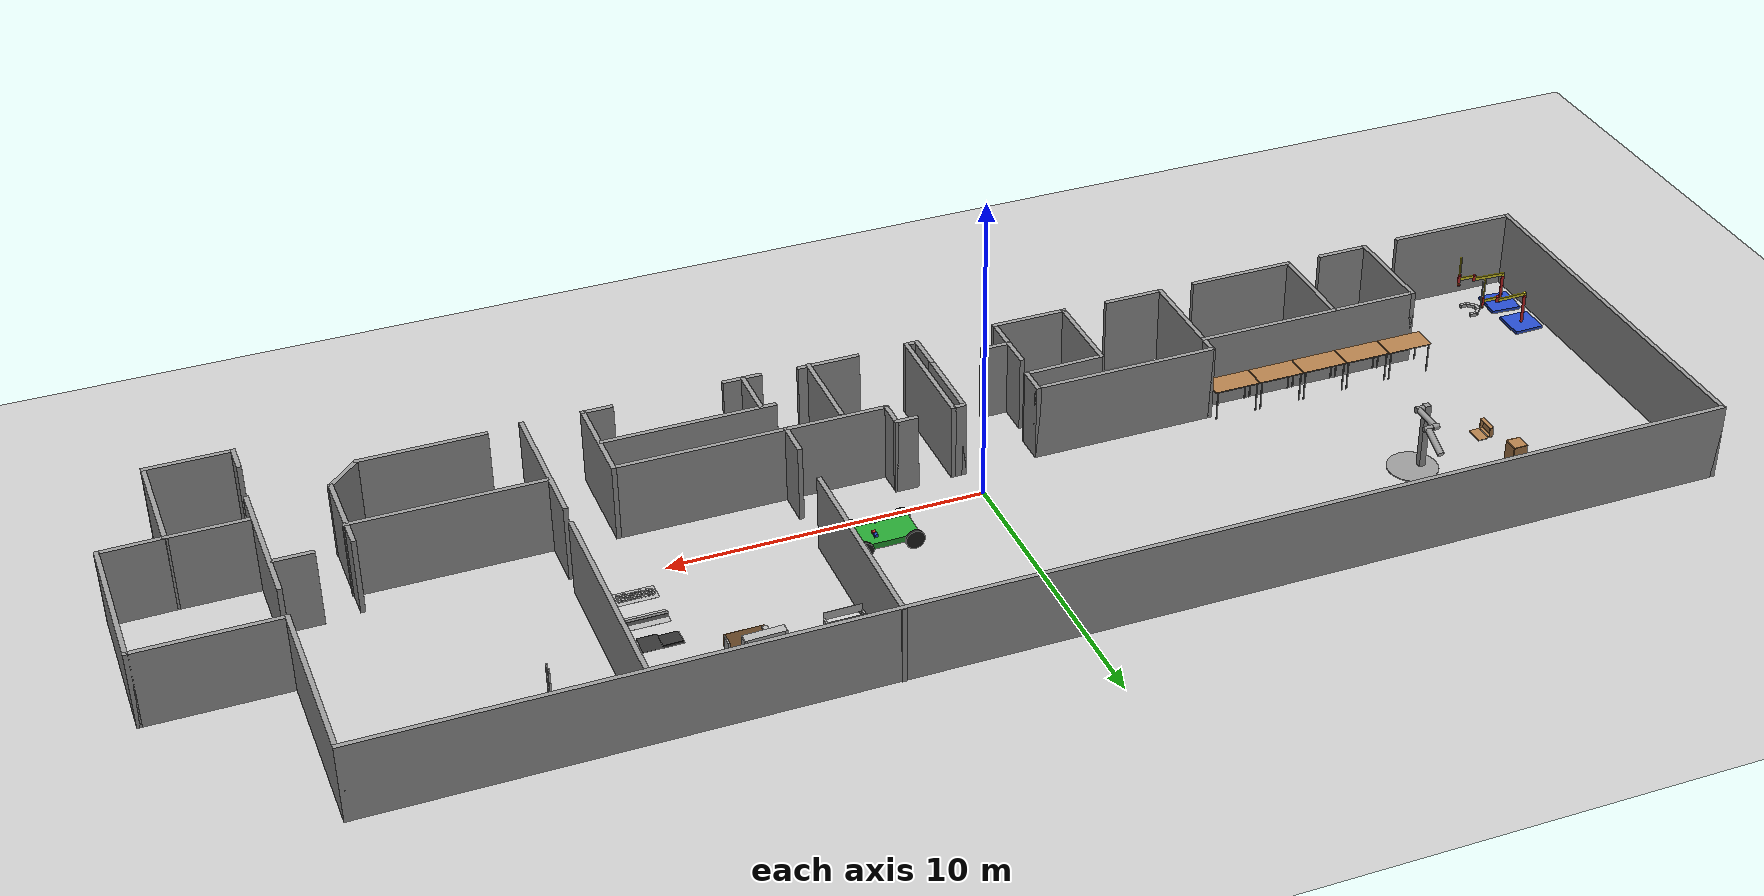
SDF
<sdf version="1.6">
 <world name="default">
  <light name="sun" type="directional">
   <pose>0 0 10 0 -0 0</pose>
   <diffuse>0.8 0.8 0.8 1</diffuse>
   <specular>0.2 0.2 0.2 1</specular>
   <attenuation>
    <range>1000</range>
    <constant>0.9</constant>
    <linear>0.01</linear>
    <quadratic>0.001</quadratic>
   </attenuation>
   <direction>-0.5 0.1 -0.9</direction>
  </light>
  <model name="ground_plane">
   <static>1</static>
   <link name="link">
    <collision name="collision">
     <geometry><plane><normal>0 0 1</normal><size>100 100</size></plane></geometry>
     <surface>
      <contact><collide_bitmask>65535</collide_bitmask></contact>
      <friction><ode><mu>100</mu><mu2>50</mu2></ode></friction>
     </surface>
    </collision>
    <visual name="visual">
     <cast_shadows>0</cast_shadows>
     <geometry><plane><normal>0 0 1</normal><size>100 100</size></plane></geometry>
     <material>
      <script><uri>file://media/materials/scripts/gazebo.material</uri><name>Gazebo/Grey</name></script>
     </material>
    </visual>
   </link>
  </model>
  <gravity>0 0 -9.8</gravity>
  <magnetic_field>6e-06 2.3e-05 -4.2e-05</magnetic_field>
  <atmosphere type="adiabatic"/>
  <physics name="default_physics" default="0" type="ode">
   <max_step_size>0.001</max_step_size>
   <real_time_factor>1</real_time_factor>
   <real_time_update_rate>1000</real_time_update_rate>
  </physics>
  <scene><ambient>0.4 0.4 0.4 1</ambient><background>0.7 0.7 0.7 1</background><shadows>1</shadows></scene>
  <spherical_coordinates>
   <surface_model>EARTH_WGS84</surface_model>
   <latitude_deg>0</latitude_deg>
   <longitude_deg>0</longitude_deg>
   <elevation>0</elevation>
   <heading_deg>0</heading_deg>
  </spherical_coordinates>
  <model name="574_3rd_floor_Labs">
   <pose>2.28282 0.192982 0 0 -0 0</pose>
   <link name="Wall_0">
    <collision name="Wall_0_Collision">
     <geometry><box><size>4.25 0.15 2.5</size></box></geometry>
     <pose>0 0 1.25 0 -0 0</pose>
    </collision>
    <visual name="Wall_0_Visual">
     <pose>0 0 1.25 0 -0 0</pose>
     <geometry><box><size>4.25 0.15 2.5</size></box></geometry>
     <material>
      <script><uri>file://media/materials/scripts/gazebo.material</uri><name>Gazebo/Grey</name></script>
      <ambient>1 1 1 1</ambient>
     </material>
     <meta><layer>0</layer></meta>
    </visual>
    <pose>-21.0506 -5.20048 0 0 -0 3.14159</pose>
   </link>
   <link name="Wall_1">
    <collision name="Wall_1_Collision">
     <geometry><box><size>12.5 0.15 2.5</size></box></geometry>
     <pose>0 0 1.25 0 -0 0</pose>
    </collision>
    <visual name="Wall_1_Visual">
     <pose>0 0 1.25 0 -0 0</pose>
     <geometry><box><size>12.5 0.15 2.5</size></box></geometry>
     <material>
      <script><uri>file://media/materials/scripts/gazebo.material</uri><name>Gazebo/Grey</name></script>
      <ambient>1 1 1 1</ambient>
     </material>
     <meta><layer>0</layer></meta>
    </visual>
    <pose>-23.1006 0.974519 0 0 -0 1.5708</pose>
   </link>
   <link name="Wall_10">
    <collision name="Wall_10_Collision">
     <geometry><box><size>1 0.15 2.5</size></box></geometry>
     <pose>0 0 1.25 0 -0 0</pose>
    </collision>
    <visual name="Wall_10_Visual">
     <pose>0 0 1.25 0 -0 0</pose>
     <geometry><box><size>1 0.15 2.5</size></box></geometry>
     <material>
      <script><uri>file://media/materials/scripts/gazebo.material</uri><name>Gazebo/Grey</name></script>
      <ambient>1 1 1 1</ambient>
     </material>
     <meta><layer>0</layer></meta>
    </visual>
    <pose>-4.55115 -1.8903 0 0 0 -1.5708</pose>
   </link>
   <link name="Wall_12">
    <collision name="Wall_12_Collision">
     <geometry><box><size>3.25 0.15 2.5</size></box></geometry>
     <pose>0 0 1.25 0 -0 0</pose>
    </collision>
    <visual name="Wall_12_Visual">
     <pose>0 0 1.25 0 -0 0</pose>
     <geometry><box><size>3.25 0.15 2.5</size></box></geometry>
     <material>
      <script><uri>file://media/materials/scripts/gazebo.material</uri><name>Gazebo/Grey</name></script>
      <ambient>1 1 1 1</ambient>
     </material>
     <meta><layer>0</layer></meta>
    </visual>
    <pose>-14.9551 -3.61957 0 0 0 -1.5708</pose>
   </link>
   <link name="Wall_13">
    <collision name="Wall_13_Collision">
     <geometry><box><size>3.5 0.15 2.5</size></box></geometry>
     <pose>0 0 1.25 0 -0 0</pose>
    </collision>
    <visual name="Wall_13_Visual">
     <pose>0 0 1.25 0 -0 0</pose>
     <geometry><box><size>3.5 0.15 2.5</size></box></geometry>
     <material>
      <script><uri>file://media/materials/scripts/gazebo.material</uri><name>Gazebo/Grey</name></script>
      <ambient>1 1 1 1</ambient>
     </material>
     <meta><layer>0</layer></meta>
    </visual>
    <pose>-13.2801 -5.16957 0 0 -0 0</pose>
   </link>
   <link name="Wall_15">
    <collision name="Wall_15_Collision">
     <geometry><box><size>3.25 0.15 2.5</size></box></geometry>
     <pose>0 0 1.25 0 -0 0</pose>
    </collision>
    <visual name="Wall_15_Visual">
     <pose>0 0 1.25 0 -0 0</pose>
     <geometry><box><size>3.25 0.15 2.5</size></box></geometry>
     <material>
      <script><uri>file://media/materials/scripts/gazebo.material</uri><name>Gazebo/Grey</name></script>
      <ambient>1 1 1 1</ambient>
     </material>
     <meta><layer>0</layer></meta>
    </visual>
    <pose>-10.4011 -3.6153 0 0 0 -1.5708</pose>
   </link>
   <link name="Wall_16">
    <collision name="Wall_16_Collision">
     <geometry><box><size>2 0.15 2.5</size></box></geometry>
     <pose>0 0 1.25 0 -0 0</pose>
    </collision>
    <visual name="Wall_16_Visual">
     <pose>0 0 1.25 0 -0 0</pose>
     <geometry><box><size>2 0.15 2.5</size></box></geometry>
     <material>
      <script><uri>file://media/materials/scripts/gazebo.material</uri><name>Gazebo/Grey</name></script>
      <ambient>1 1 1 1</ambient>
     </material>
     <meta><layer>0</layer></meta>
    </visual>
    <pose>-9.47615 -5.1653 0 0 -0 0</pose>
   </link>
   <link name="Wall_18">
    <collision name="Wall_18_Collision">
     <geometry><box><size>2.25 0.15 2.5</size></box></geometry>
     <pose>0 0 1.25 0 -0 0</pose>
    </collision>
    <visual name="Wall_18_Visual">
     <pose>0 0 1.25 0 -0 0</pose>
     <geometry><box><size>2.25 0.15 2.5</size></box></geometry>
     <material>
      <script><uri>file://media/materials/scripts/gazebo.material</uri><name>Gazebo/Grey</name></script>
      <ambient>1 1 1 1</ambient>
     </material>
     <meta><layer>0</layer></meta>
    </visual>
    <pose>-4.71805 -4.17493 0 0 0 -1.5708</pose>
   </link>
   <link name="Wall_19">
    <collision name="Wall_19_Collision">
     <geometry><box><size>2.5 0.15 2.5</size></box></geometry>
     <pose>0 0 1.25 0 -0 0</pose>
    </collision>
    <visual name="Wall_19_Visual">
     <pose>0 0 1.25 0 -0 0</pose>
     <geometry><box><size>2.5 0.15 2.5</size></box></geometry>
     <material>
      <script><uri>file://media/materials/scripts/gazebo.material</uri><name>Gazebo/Grey</name></script>
      <ambient>1 1 1 1</ambient>
     </material>
     <meta><layer>0</layer></meta>
    </visual>
    <pose>-5.89305 -5.22493 0 0 -0 3.14159</pose>
   </link>
   <link name="Wall_2">
    <collision name="Wall_2_Collision">
     <geometry><box><size>42 0.15 2.5</size></box></geometry>
     <pose>0 0 1.25 0 -0 0</pose>
    </collision>
    <visual name="Wall_2_Visual">
     <pose>0 0 1.25 0 -0 0</pose>
     <geometry><box><size>42 0.15 2.5</size></box></geometry>
     <material>
      <script><uri>file://media/materials/scripts/gazebo.material</uri><name>Gazebo/Grey</name></script>
      <ambient>1 1 1 1</ambient>
     </material>
     <meta><layer>0</layer></meta>
    </visual>
    <pose>-2.17563 7.14952 0 0 -0 0</pose>
   </link>
   <link name="Wall_20">
    <collision name="Wall_20_Collision">
     <geometry><box><size>3 0.15 2.5</size></box></geometry>
     <pose>0 0 1.25 0 -0 0</pose>
    </collision>
    <visual name="Wall_20_Visual">
     <pose>0 0 1.25 0 -0 0</pose>
     <geometry><box><size>3 0.15 2.5</size></box></geometry>
     <material>
      <script><uri>file://media/materials/scripts/gazebo.material</uri><name>Gazebo/Grey</name></script>
      <ambient>1 1 1 1</ambient>
     </material>
     <meta><layer>0</layer></meta>
    </visual>
    <pose>-7.06805 -3.79993 0 0 -0 1.5708</pose>
   </link>
   <link name="Wall_21">
    <collision name="Wall_21_Collision">
     <geometry><box><size>2.66761 0.15 2.5</size></box></geometry>
     <pose>0 0 1.25 0 -0 0</pose>
    </collision>
    <visual name="Wall_21_Visual">
     <pose>0 0 1.25 0 -0 0</pose>
     <geometry><box><size>2.66761 0.15 2.5</size></box></geometry>
     <material>
      <script><uri>file://media/materials/scripts/gazebo.material</uri><name>Gazebo/Grey</name></script>
      <ambient>1 1 1 1</ambient>
     </material>
     <meta><layer>0</layer></meta>
    </visual>
    <pose>-5.8096 -2.34512 0 0 -0 0.023688</pose>
   </link>
   <link name="Wall_24">
    <collision name="Wall_24_Collision">
     <geometry><box><size>6.75 0.15 2.5</size></box></geometry>
     <pose>0 0 1.25 0 -0 0</pose>
    </collision>
    <visual name="Wall_24_Visual">
     <pose>0 0 1.25 0 -0 0</pose>
     <geometry><box><size>6.75 0.15 2.5</size></box></geometry>
     <material>
      <script><uri>file://media/materials/scripts/gazebo.material</uri><name>Gazebo/Grey</name></script>
      <ambient>1 1 1 1</ambient>
     </material>
     <meta><layer>0</layer></meta>
    </visual>
    <pose>3.19717 3.88244 0 0 0 -1.5708</pose>
   </link>
   <link name="Wall_26">
    <collision name="Wall_26_Collision">
     <geometry><box><size>7.25 0.15 2.5</size></box></geometry>
     <pose>0 0 1.25 0 -0 0</pose>
    </collision>
    <visual name="Wall_26_Visual">
     <pose>0 0 1.25 0 -0 0</pose>
     <geometry><box><size>7.25 0.15 2.5</size></box></geometry>
     <material>
      <script><uri>file://media/materials/scripts/gazebo.material</uri><name>Gazebo/Grey</name></script>
      <ambient>1 1 1 1</ambient>
     </material>
     <meta><layer>0</layer></meta>
    </visual>
    <pose>10.444 3.56209 0 0 0 -1.5708</pose>
   </link>
   <link name="Wall_28">
    <collision name="Wall_28_Collision">
     <geometry><box><size>1 0.15 2.5</size></box></geometry>
     <pose>0 0 1.25 0 -0 0</pose>
    </collision>
    <visual name="Wall_28_Visual">
     <pose>0 0 1.25 0 -0 0</pose>
     <geometry><box><size>1 0.15 2.5</size></box></geometry>
     <material>
      <script><uri>file://media/materials/scripts/gazebo.material</uri><name>Gazebo/Grey</name></script>
      <ambient>1 1 1 1</ambient>
     </material>
     <meta><layer>0</layer></meta>
    </visual>
    <pose>-4.29305 -4.10994 0 0 -0 0</pose>
   </link>
   <link name="Wall_3">
    <collision name="Wall_3_Collision">
     <geometry><box><size>6 0.15 2.5</size></box></geometry>
     <pose>0 0 1.25 0 -0 0</pose>
    </collision>
    <visual name="Wall_3_Visual">
     <pose>0 0 1.25 0 -0 0</pose>
     <geometry><box><size>6 0.15 2.5</size></box></geometry>
     <material>
      <script><uri>file://media/materials/scripts/gazebo.material</uri><name>Gazebo/Grey</name></script>
      <ambient>1 1 1 1</ambient>
     </material>
     <meta><layer>0</layer></meta>
    </visual>
    <pose>18.7494 4.22452 0 0 0 -1.5708</pose>
   </link>
   <link name="Wall_30">
    <collision name="Wall_30_Collision">
     <geometry><box><size>2.75 0.15 2.5</size></box></geometry>
     <pose>0 0 1.25 0 -0 0</pose>
    </collision>
    <visual name="Wall_30_Visual">
     <pose>0 0 1.25 0 -0 0</pose>
     <geometry><box><size>2.75 0.15 2.5</size></box></geometry>
     <material>
      <script><uri>file://media/materials/scripts/gazebo.material</uri><name>Gazebo/Grey</name></script>
      <ambient>1 1 1 1</ambient>
     </material>
     <meta><layer>0</layer></meta>
    </visual>
    <pose>-2.11482 -2.73958 0 0 -0 1.5708</pose>
   </link>
   <link name="Wall_31">
    <collision name="Wall_31_Collision">
     <geometry><box><size>0.5 0.15 2.5</size></box></geometry>
     <pose>0 0 1.25 0 -0 0</pose>
    </collision>
    <visual name="Wall_31_Visual">
     <pose>0 0 1.25 0 -0 0</pose>
     <geometry><box><size>0.5 0.15 2.5</size></box></geometry>
     <material>
      <script><uri>file://media/materials/scripts/gazebo.material</uri><name>Gazebo/Grey</name></script>
      <ambient>1 1 1 1</ambient>
     </material>
     <meta><layer>0</layer></meta>
    </visual>
    <pose>-1.93982 -1.43958 0 0 -0 0</pose>
   </link>
   <link name="Wall_32">
    <collision name="Wall_32_Collision">
     <geometry><box><size>3.92964 0.15 2.5</size></box></geometry>
     <pose>0 0 1.25 0 -0 0</pose>
    </collision>
    <visual name="Wall_32_Visual">
     <pose>0 0 1.25 0 -0 0</pose>
     <geometry><box><size>3.92964 0.15 2.5</size></box></geometry>
     <material>
      <script><uri>file://media/materials/scripts/gazebo.material</uri><name>Gazebo/Grey</name></script>
      <ambient>1 1 1 1</ambient>
     </material>
     <meta><layer>0</layer></meta>
    </visual>
    <pose>-1.76482 -3.3294 0 0 0 -1.5708</pose>
   </link>
   <link name="Wall_35">
    <collision name="Wall_35_Collision">
     <geometry><box><size>0.5 0.15 2.5</size></box></geometry>
     <pose>0 0 1.25 0 -0 0</pose>
    </collision>
    <visual name="Wall_35_Visual">
     <pose>0 0 1.25 0 -0 0</pose>
     <geometry><box><size>0.5 0.15 2.5</size></box></geometry>
     <material>
      <script><uri>file://media/materials/scripts/gazebo.material</uri><name>Gazebo/Grey</name></script>
      <ambient>1 1 1 1</ambient>
     </material>
     <meta><layer>0</layer></meta>
    </visual>
    <pose>-1.93982 -5.21922 0 0 -0 3.14159</pose>
   </link>
   <link name="Wall_36">
    <collision name="Wall_36_Collision">
     <geometry><box><size>1.32964 0.15 2.5</size></box></geometry>
     <pose>0 0 1.25 0 -0 0</pose>
    </collision>
    <visual name="Wall_36_Visual">
     <pose>0 0 1.25 0 -0 0</pose>
     <geometry><box><size>1.32964 0.15 2.5</size></box></geometry>
     <material>
      <script><uri>file://media/materials/scripts/gazebo.material</uri><name>Gazebo/Grey</name></script>
      <ambient>1 1 1 1</ambient>
     </material>
     <meta><layer>0</layer></meta>
    </visual>
    <pose>-2.11482 -4.6294 0 0 -0 1.5708</pose>
   </link>
   <link name="Wall_38">
    <collision name="Wall_38_Collision">
     <geometry><box><size>4.75 0.15 2.5</size></box></geometry>
     <pose>0 0 1.25 0 -0 0</pose>
    </collision>
    <visual name="Wall_38_Visual">
     <pose>0 0 1.25 0 -0 0</pose>
     <geometry><box><size>4.75 0.15 2.5</size></box></geometry>
     <material>
      <script><uri>file://media/materials/scripts/gazebo.material</uri><name>Gazebo/Grey</name></script>
      <ambient>1 1 1 1</ambient>
     </material>
     <meta><layer>0</layer></meta>
    </visual>
    <pose>10.4088 -3.10313 0 0 0 -1.5708</pose>
   </link>
   <link name="Wall_40">
    <collision name="Wall_40_Collision">
     <geometry><box><size>2 0.15 2.5</size></box></geometry>
     <pose>0 0 1.25 0 -0 0</pose>
    </collision>
    <visual name="Wall_40_Visual">
     <pose>0 0 1.25 0 -0 0</pose>
     <geometry><box><size>2 0.15 2.5</size></box></geometry>
     <material>
      <script><uri>file://media/materials/scripts/gazebo.material</uri><name>Gazebo/Grey</name></script>
      <ambient>1 1 1 1</ambient>
     </material>
     <meta><layer>0</layer></meta>
    </visual>
    <pose>0.819218 -5.19149 0 0 -0 0</pose>
   </link>
   <link name="Wall_42">
    <collision name="Wall_42_Collision">
     <geometry><box><size>3 0.15 2.5</size></box></geometry>
     <pose>0 0 1.25 0 -0 0</pose>
    </collision>
    <visual name="Wall_42_Visual">
     <pose>0 0 1.25 0 -0 0</pose>
     <geometry><box><size>3 0.15 2.5</size></box></geometry>
     <material>
      <script><uri>file://media/materials/scripts/gazebo.material</uri><name>Gazebo/Grey</name></script>
      <ambient>1 1 1 1</ambient>
     </material>
     <meta><layer>0</layer></meta>
    </visual>
    <pose>1.44208 -3.80167 0 0 -0 1.5708</pose>
   </link>
   <link name="Wall_44">
    <collision name="Wall_44_Collision">
     <geometry><box><size>8.5 0.15 2.5</size></box></geometry>
     <pose>0 0 1.25 0 -0 0</pose>
    </collision>
    <visual name="Wall_44_Visual">
     <pose>0 0 1.25 0 -0 0</pose>
     <geometry><box><size>8.5 0.15 2.5</size></box></geometry>
     <material>
      <script><uri>file://media/materials/scripts/gazebo.material</uri><name>Gazebo/Grey</name></script>
      <ambient>1 1 1 1</ambient>
     </material>
     <meta><layer>0</layer></meta>
    </visual>
    <pose>4.24511 -2.2013 0 0 -0 0</pose>
   </link>
   <link name="Wall_46">
    <collision name="Wall_46_Collision">
     <geometry><box><size>1 0.15 2.5</size></box></geometry>
     <pose>0 0 1.25 0 -0 0</pose>
    </collision>
    <visual name="Wall_46_Visual">
     <pose>0 0 1.25 0 -0 0</pose>
     <geometry><box><size>1 0.15 2.5</size></box></geometry>
     <material>
      <script><uri>file://media/materials/scripts/gazebo.material</uri><name>Gazebo/Grey</name></script>
      <ambient>1 1 1 1</ambient>
     </material>
     <meta><layer>0</layer></meta>
    </visual>
    <pose>8.1289 -5.29703 0 0 -0 0</pose>
   </link>
   <link name="Wall_47">
    <collision name="Wall_47_Collision">
     <geometry><box><size>3.25 0.15 2.5</size></box></geometry>
     <pose>0 0 1.25 0 -0 0</pose>
    </collision>
    <visual name="Wall_47_Visual">
     <pose>0 0 1.25 0 -0 0</pose>
     <geometry><box><size>3.25 0.15 2.5</size></box></geometry>
     <material>
      <script><uri>file://media/materials/scripts/gazebo.material</uri><name>Gazebo/Grey</name></script>
      <ambient>1 1 1 1</ambient>
     </material>
     <meta><layer>0</layer></meta>
    </visual>
    <pose>8.5539 -3.74703 0 0 -0 1.5708</pose>
   </link>
   <link name="Wall_5">
    <collision name="Wall_5_Collision">
     <geometry><box><size>1.75 0.15 2.5</size></box></geometry>
     <pose>0 0 1.25 0 -0 0</pose>
    </collision>
    <visual name="Wall_5_Visual">
     <pose>0 0 1.25 0 -0 0</pose>
     <geometry><box><size>1.75 0.15 2.5</size></box></geometry>
     <material>
      <script><uri>file://media/materials/scripts/gazebo.material</uri><name>Gazebo/Grey</name></script>
      <ambient>1 1 1 1</ambient>
     </material>
     <meta><layer>0</layer></meta>
    </visual>
    <pose>-16.9511 -5.1653 0 0 -0 3.14159</pose>
   </link>
   <link name="Wall_50">
    <collision name="Wall_50_Collision">
     <geometry><box><size>4 0.15 2.5</size></box></geometry>
     <pose>0 0 1.25 0 -0 0</pose>
    </collision>
    <visual name="Wall_50_Visual">
     <pose>0 0 1.25 0 -0 0</pose>
     <geometry><box><size>4 0.15 2.5</size></box></geometry>
     <material>
      <script><uri>file://media/materials/scripts/gazebo.material</uri><name>Gazebo/Grey</name></script>
      <ambient>1 1 1 1</ambient>
     </material>
     <meta><layer>0</layer></meta>
    </visual>
    <pose>13.4634 -5.29703 0 0 -0 0</pose>
   </link>
   <link name="Wall_53">
    <collision name="Wall_53_Collision">
     <geometry><box><size>1.5 0.15 2.5</size></box></geometry>
     <pose>0 0 1.25 0 -0 0</pose>
    </collision>
    <visual name="Wall_53_Visual">
     <pose>0 0 1.25 0 -0 0</pose>
     <geometry><box><size>1.5 0.15 2.5</size></box></geometry>
     <material>
      <script><uri>file://media/materials/scripts/gazebo.material</uri><name>Gazebo/Grey</name></script>
      <ambient>1 1 1 1</ambient>
     </material>
     <meta><layer>0</layer></meta>
    </visual>
    <pose>15.8657 -4.81973 0 0 -0 0.785398</pose>
   </link>
   <link name="Wall_54">
    <collision name="Wall_54_Collision">
     <geometry><box><size>3 0.15 2.5</size></box></geometry>
     <pose>0 0 1.25 0 -0 0</pose>
    </collision>
    <visual name="Wall_54_Visual">
     <pose>0 0 1.25 0 -0 0</pose>
     <geometry><box><size>3 0.15 2.5</size></box></geometry>
     <material>
      <script><uri>file://media/materials/scripts/gazebo.material</uri><name>Gazebo/Grey</name></script>
      <ambient>1 1 1 1</ambient>
     </material>
     <meta><layer>0</layer></meta>
    </visual>
    <pose>16.343 -2.91743 0 0 -0 1.5708</pose>
   </link>
   <link name="Wall_56">
    <collision name="Wall_56_Collision">
     <geometry><box><size>1.25 0.15 2.5</size></box></geometry>
     <pose>0 0 1.25 0 -0 0</pose>
    </collision>
    <visual name="Wall_56_Visual">
     <pose>0 0 1.25 0 -0 0</pose>
     <geometry><box><size>1.25 0.15 2.5</size></box></geometry>
     <material>
      <script><uri>file://media/materials/scripts/gazebo.material</uri><name>Gazebo/Grey</name></script>
      <ambient>1 1 1 1</ambient>
     </material>
     <meta><layer>0</layer></meta>
    </visual>
    <pose>18.0688 -1.35701 0 0 -0 0</pose>
   </link>
   <link name="Wall_58">
    <collision name="Wall_58_Collision">
     <geometry><box><size>4.75 0.15 2.5</size></box></geometry>
     <pose>0 0 1.25 0 -0 0</pose>
    </collision>
    <visual name="Wall_58_Visual">
     <pose>0 0 1.25 0 -0 0</pose>
     <geometry><box><size>4.75 0.15 2.5</size></box></geometry>
     <material>
      <script><uri>file://media/materials/scripts/gazebo.material</uri><name>Gazebo/Grey</name></script>
      <ambient>1 1 1 1</ambient>
     </material>
     <meta><layer>0</layer></meta>
    </visual>
    <pose>18.7149 -2.35539 0 0 0 -1.5708</pose>
   </link>
   <link name="Wall_6">
    <collision name="Wall_6_Collision">
     <geometry><box><size>3.25 0.15 2.5</size></box></geometry>
     <pose>0 0 1.25 0 -0 0</pose>
    </collision>
    <visual name="Wall_6_Visual">
     <pose>0 0 1.25 0 -0 0</pose>
     <geometry><box><size>3.25 0.15 2.5</size></box></geometry>
     <material>
      <script><uri>file://media/materials/scripts/gazebo.material</uri><name>Gazebo/Grey</name></script>
      <ambient>1 1 1 1</ambient>
     </material>
     <meta><layer>0</layer></meta>
    </visual>
    <pose>-17.7511 -3.6153 0 0 -0 1.5708</pose>
   </link>
   <link name="Wall_60">
    <collision name="Wall_60_Collision">
     <geometry><box><size>2.5 0.15 2.5</size></box></geometry>
     <pose>0 0 1.25 0 -0 0</pose>
    </collision>
    <visual name="Wall_60_Visual">
     <pose>0 0 1.25 0 -0 0</pose>
     <geometry><box><size>2.5 0.15 2.5</size></box></geometry>
     <material>
      <script><uri>file://media/materials/scripts/gazebo.material</uri><name>Gazebo/Grey</name></script>
      <ambient>1 1 1 1</ambient>
     </material>
     <meta><layer>0</layer></meta>
    </visual>
    <pose>20.0332 -3.58244 0 0 -0 0</pose>
   </link>
   <link name="Wall_61">
    <collision name="Wall_61_Collision">
     <geometry><box><size>3.75 0.15 2.5</size></box></geometry>
     <pose>0 0 1.25 0 -0 0</pose>
    </collision>
    <visual name="Wall_61_Visual">
     <pose>0 0 1.25 0 -0 0</pose>
     <geometry><box><size>3.75 0.15 2.5</size></box></geometry>
     <material>
      <script><uri>file://media/materials/scripts/gazebo.material</uri><name>Gazebo/Grey</name></script>
      <ambient>1 1 1 1</ambient>
     </material>
     <meta><layer>0</layer></meta>
    </visual>
    <pose>21.2082 -5.38244 0 0 0 -1.5708</pose>
   </link>
   <link name="Wall_62">
    <collision name="Wall_62_Collision">
     <geometry><box><size>2.75 0.15 2.5</size></box></geometry>
     <pose>0 0 1.25 0 -0 0</pose>
    </collision>
    <visual name="Wall_62_Visual">
     <pose>0 0 1.25 0 -0 0</pose>
     <geometry><box><size>2.75 0.15 2.5</size></box></geometry>
     <material>
      <script><uri>file://media/materials/scripts/gazebo.material</uri><name>Gazebo/Grey</name></script>
      <ambient>1 1 1 1</ambient>
     </material>
     <meta><layer>0</layer></meta>
    </visual>
    <pose>19.9082 -7.18244 0 0 -0 3.14159</pose>
   </link>
   <link name="Wall_63">
    <collision name="Wall_63_Collision">
     <geometry><box><size>1 0.15 2.5</size></box></geometry>
     <pose>0 0 1.25 0 -0 0</pose>
    </collision>
    <visual name="Wall_63_Visual">
     <pose>0 0 1.25 0 -0 0</pose>
     <geometry><box><size>1 0.15 2.5</size></box></geometry>
     <material>
      <script><uri>file://media/materials/scripts/gazebo.material</uri><name>Gazebo/Grey</name></script>
      <ambient>1 1 1 1</ambient>
     </material>
     <meta><layer>0</layer></meta>
    </visual>
    <pose>18.6082 -6.75744 0 0 -0 1.5708</pose>
   </link>
   <link name="Wall_65">
    <collision name="Wall_65_Collision">
     <geometry><box><size>4.5 0.15 2.5</size></box></geometry>
     <pose>0 0 1.25 0 -0 0</pose>
    </collision>
    <visual name="Wall_65_Visual">
     <pose>0 0 1.25 0 -0 0</pose>
     <geometry><box><size>4.5 0.15 2.5</size></box></geometry>
     <material>
      <script><uri>file://media/materials/scripts/gazebo.material</uri><name>Gazebo/Grey</name></script>
      <ambient>1 1 1 1</ambient>
     </material>
     <meta><layer>0</layer></meta>
    </visual>
    <pose>20.9244 1.29952 0 0 -0 0</pose>
   </link>
   <link name="Wall_66">
    <collision name="Wall_66_Collision">
     <geometry><box><size>5 0.15 2.5</size></box></geometry>
     <pose>0 0 1.25 0 -0 0</pose>
    </collision>
    <visual name="Wall_66_Visual">
     <pose>0 0 1.25 0 -0 0</pose>
     <geometry><box><size>5 0.15 2.5</size></box></geometry>
     <material>
      <script><uri>file://media/materials/scripts/gazebo.material</uri><name>Gazebo/Grey</name></script>
      <ambient>1 1 1 1</ambient>
     </material>
     <meta><layer>0</layer></meta>
    </visual>
    <pose>23.0994 -1.12548 0 0 0 -1.5708</pose>
   </link>
   <link name="Wall_67">
    <collision name="Wall_67_Collision">
     <geometry><box><size>2.04146 0.15 2.5</size></box></geometry>
     <pose>0 0 1.25 0 -0 0</pose>
    </collision>
    <visual name="Wall_67_Visual">
     <pose>0 0 1.25 0 -0 0</pose>
     <geometry><box><size>2.04146 0.15 2.5</size></box></geometry>
     <material>
      <script><uri>file://media/materials/scripts/gazebo.material</uri><name>Gazebo/Grey</name></script>
      <ambient>1 1 1 1</ambient>
     </material>
     <meta><layer>0</layer></meta>
    </visual>
    <pose>22.1538 -3.56646 0 0 0 -3.12469</pose>
   </link>
   <link name="Wall_69">
    <collision name="Wall_69_Collision">
     <geometry><box><size>1 0.15 2.5</size></box></geometry>
     <pose>0 0 1.25 0 -0 0</pose>
    </collision>
    <visual name="Wall_69_Visual">
     <pose>0 0 1.25 0 -0 0</pose>
     <geometry><box><size>1 0.15 2.5</size></box></geometry>
     <material>
      <script><uri>file://media/materials/scripts/gazebo.material</uri><name>Gazebo/Grey</name></script>
      <ambient>1 1 1 1</ambient>
     </material>
     <meta><layer>0</layer></meta>
    </visual>
    <pose>0.070112 -1.7763 0 0 -0 1.5708</pose>
   </link>
   <link name="Wall_7">
    <collision name="Wall_7_Collision">
     <geometry><box><size>7.5 0.15 2.5</size></box></geometry>
     <pose>0 0 1.25 0 -0 0</pose>
    </collision>
    <visual name="Wall_7_Visual">
     <pose>0 0 1.25 0 -0 0</pose>
     <geometry><box><size>7.5 0.15 2.5</size></box></geometry>
     <material>
      <script><uri>file://media/materials/scripts/gazebo.material</uri><name>Gazebo/Grey</name></script>
      <ambient>1 1 1 1</ambient>
     </material>
     <meta><layer>0</layer></meta>
    </visual>
    <pose>-14.0761 -2.0653 0 0 -0 0</pose>
   </link>
   <link name="Wall_70">
    <collision name="Wall_70_Collision">
     <geometry><box><size>0.75 0.15 2.5</size></box></geometry>
     <pose>0 0 1.25 0 -0 0</pose>
    </collision>
    <visual name="Wall_70_Visual">
     <pose>0 0 1.25 0 -0 0</pose>
     <geometry><box><size>0.75 0.15 2.5</size></box></geometry>
     <material>
      <script><uri>file://media/materials/scripts/gazebo.material</uri><name>Gazebo/Grey</name></script>
      <ambient>1 1 1 1</ambient>
     </material>
     <meta><layer>0</layer></meta>
    </visual>
    <pose>-0.229888 -1.3513 0 0 -0 3.14159</pose>
   </link>
   <link name="Wall_72">
    <collision name="Wall_72_Collision">
     <geometry><box><size>1.25 0.15 2.5</size></box></geometry>
     <pose>0 0 1.25 0 -0 0</pose>
    </collision>
    <visual name="Wall_72_Visual">
     <pose>0 0 1.25 0 -0 0</pose>
     <geometry><box><size>1.25 0.15 2.5</size></box></geometry>
     <material>
      <script><uri>file://media/materials/scripts/gazebo.material</uri><name>Gazebo/Grey</name></script>
      <ambient>1 1 1 1</ambient>
     </material>
     <meta><layer>0</layer></meta>
    </visual>
    <pose>3.56558 -5.29474 0 0 -0 0</pose>
   </link>
   <link name="Wall_74">
    <collision name="Wall_74_Collision">
     <geometry><box><size>5.5 0.15 2.5</size></box></geometry>
     <pose>0 0 1.25 0 -0 0</pose>
    </collision>
    <visual name="Wall_74_Visual">
     <pose>0 0 1.25 0 -0 0</pose>
     <geometry><box><size>5.5 0.15 2.5</size></box></geometry>
     <material>
      <script><uri>file://media/materials/scripts/gazebo.material</uri><name>Gazebo/Grey</name></script>
      <ambient>1 1 1 1</ambient>
     </material>
     <meta><layer>0</layer></meta>
    </visual>
    <pose>5.81294 -3.58168 0 0 -0 0</pose>
   </link>
   <link name="Wall_76">
    <collision name="Wall_76_Collision">
     <geometry><box><size>1.75 0.15 2.5</size></box></geometry>
     <pose>0 0 1.25 0 -0 0</pose>
    </collision>
    <visual name="Wall_76_Visual">
     <pose>0 0 1.25 0 -0 0</pose>
     <geometry><box><size>1.75 0.15 2.5</size></box></geometry>
     <material>
      <script><uri>file://media/materials/scripts/gazebo.material</uri><name>Gazebo/Grey</name></script>
      <ambient>1 1 1 1</ambient>
     </material>
     <meta><layer>0</layer></meta>
    </visual>
    <pose>3.53562 -4.46415 0 0 -0 1.5708</pose>
   </link>
   <link name="Wall_78">
    <collision name="Wall_78_Collision">
     <geometry><box><size>1.25 0.15 2.5</size></box></geometry>
     <pose>0 0 1.25 0 -0 0</pose>
    </collision>
    <visual name="Wall_78_Visual">
     <pose>0 0 1.25 0 -0 0</pose>
     <geometry><box><size>1.25 0.15 2.5</size></box></geometry>
     <material>
      <script><uri>file://media/materials/scripts/gazebo.material</uri><name>Gazebo/Grey</name></script>
      <ambient>1 1 1 1</ambient>
     </material>
     <meta><layer>0</layer></meta>
    </visual>
    <pose>3.22971 -1.65512 0 0 -0 1.5708</pose>
   </link>
   <link name="Wall_8">
    <collision name="Wall_8_Collision">
     <geometry><box><size>0.75 0.15 2.5</size></box></geometry>
     <pose>0 0 1.25 0 -0 0</pose>
    </collision>
    <visual name="Wall_8_Visual">
     <pose>0 0 1.25 0 -0 0</pose>
     <geometry><box><size>0.75 0.15 2.5</size></box></geometry>
     <material>
      <script><uri>file://media/materials/scripts/gazebo.material</uri><name>Gazebo/Grey</name></script>
      <ambient>1 1 1 1</ambient>
     </material>
     <meta><layer>0</layer></meta>
    </visual>
    <pose>-10.4011 -1.7653 0 0 -0 1.5708</pose>
   </link>
   <link name="Wall_80">
    <collision name="Wall_80_Collision">
     <geometry><box><size>6 0.15 2.5</size></box></geometry>
     <pose>0 0 1.25 0 -0 0</pose>
    </collision>
    <visual name="Wall_80_Visual">
     <pose>0 0 1.25 0 -0 0</pose>
     <geometry><box><size>6 0.15 2.5</size></box></geometry>
     <material>
      <script><uri>file://media/materials/scripts/gazebo.material</uri><name>Gazebo/Grey</name></script>
      <ambient>1 1 1 1</ambient>
     </material>
     <meta><layer>0</layer></meta>
    </visual>
    <pose>13.453 -2.3154 0 0 -0 3.14159</pose>
   </link>
   <link name="Wall_9">
    <collision name="Wall_9_Collision">
     <geometry><box><size>6 0.15 2.5</size></box></geometry>
     <pose>0 0 1.25 0 -0 0</pose>
    </collision>
    <visual name="Wall_9_Visual">
     <pose>0 0 1.25 0 -0 0</pose>
     <geometry><box><size>6 0.15 2.5</size></box></geometry>
     <material>
      <script><uri>file://media/materials/scripts/gazebo.material</uri><name>Gazebo/Grey</name></script>
      <ambient>1 1 1 1</ambient>
     </material>
     <meta><layer>0</layer></meta>
    </visual>
    <pose>-7.47615 -1.4653 0 0 -0 0</pose>
   </link>
   <static>1</static>
  </model>
  <model name="table">
   <static>1</static>
   <link name="link">
    <collision name="surface">
     <pose>0 0 1 0 -0 0</pose>
     <geometry><box><size>1.5 0.8 0.03</size></box></geometry>
     <surface><friction><ode><mu>0.6</mu><mu2>0.6</mu2></ode></friction></surface>
    </collision>
    <visual name="visual1">
     <pose>0 0 1 0 -0 0</pose>
     <geometry><box><size>1.5 0.8 0.03</size></box></geometry>
     <material>
      <script><uri>file://media/materials/scripts/gazebo.material</uri><name>Gazebo/Wood</name></script>
     </material>
    </visual>
    <collision name="front_left_leg">
     <pose>0.68 0.38 0.5 0 -0 0</pose>
     <geometry><cylinder><radius>0.02</radius><length>1</length></cylinder></geometry>
    </collision>
    <visual name="front_left_leg">
     <pose>0.68 0.38 0.5 0 -0 0</pose>
     <geometry><cylinder><radius>0.02</radius><length>1</length></cylinder></geometry>
     <material>
      <script><uri>file://media/materials/scripts/gazebo.material</uri><name>Gazebo/Grey</name></script>
     </material>
    </visual>
    <collision name="front_right_leg">
     <pose>0.68 -0.38 0.5 0 -0 0</pose>
     <geometry><cylinder><radius>0.02</radius><length>1</length></cylinder></geometry>
    </collision>
    <visual name="front_right_leg">
     <pose>0.68 -0.38 0.5 0 -0 0</pose>
     <geometry><cylinder><radius>0.02</radius><length>1</length></cylinder></geometry>
     <material>
      <script><uri>file://media/materials/scripts/gazebo.material</uri><name>Gazebo/Grey</name></script>
     </material>
    </visual>
    <collision name="back_right_leg">
     <pose>-0.68 -0.38 0.5 0 -0 0</pose>
     <geometry><cylinder><radius>0.02</radius><length>1</length></cylinder></geometry>
    </collision>
    <visual name="back_right_leg">
     <pose>-0.68 -0.38 0.5 0 -0 0</pose>
     <geometry><cylinder><radius>0.02</radius><length>1</length></cylinder></geometry>
     <material>
      <script><uri>file://media/materials/scripts/gazebo.material</uri><name>Gazebo/Grey</name></script>
     </material>
    </visual>
    <collision name="back_left_leg">
     <pose>-0.68 0.38 0.5 0 -0 0</pose>
     <geometry><cylinder><radius>0.02</radius><length>1</length></cylinder></geometry>
    </collision>
    <visual name="back_left_leg">
     <pose>-0.68 0.38 0.5 0 -0 0</pose>
     <geometry><cylinder><radius>0.02</radius><length>1</length></cylinder></geometry>
     <material>
      <script><uri>file://media/materials/scripts/gazebo.material</uri><name>Gazebo/Grey</name></script>
     </material>
    </visual>
   </link>
   <pose>-8.95807 -1.39202 0 0 -0 0</pose>
  </model>
  <model name="table_0">
   <static>1</static>
   <link name="link">
    <collision name="surface">
     <pose>0 0 1 0 -0 0</pose>
     <geometry><box><size>1.5 0.8 0.03</size></box></geometry>
     <surface><friction><ode><mu>0.6</mu><mu2>0.6</mu2></ode></friction></surface>
    </collision>
    <visual name="visual1">
     <pose>0 0 1 0 -0 0</pose>
     <geometry><box><size>1.5 0.8 0.03</size></box></geometry>
     <material>
      <script><uri>file://media/materials/scripts/gazebo.material</uri><name>Gazebo/Wood</name></script>
     </material>
    </visual>
    <collision name="front_left_leg">
     <pose>0.68 0.38 0.5 0 -0 0</pose>
     <geometry><cylinder><radius>0.02</radius><length>1</length></cylinder></geometry>
    </collision>
    <visual name="front_left_leg">
     <pose>0.68 0.38 0.5 0 -0 0</pose>
     <geometry><cylinder><radius>0.02</radius><length>1</length></cylinder></geometry>
     <material>
      <script><uri>file://media/materials/scripts/gazebo.material</uri><name>Gazebo/Grey</name></script>
     </material>
    </visual>
    <collision name="front_right_leg">
     <pose>0.68 -0.38 0.5 0 -0 0</pose>
     <geometry><cylinder><radius>0.02</radius><length>1</length></cylinder></geometry>
    </collision>
    <visual name="front_right_leg">
     <pose>0.68 -0.38 0.5 0 -0 0</pose>
     <geometry><cylinder><radius>0.02</radius><length>1</length></cylinder></geometry>
     <material>
      <script><uri>file://media/materials/scripts/gazebo.material</uri><name>Gazebo/Grey</name></script>
     </material>
    </visual>
    <collision name="back_right_leg">
     <pose>-0.68 -0.38 0.5 0 -0 0</pose>
     <geometry><cylinder><radius>0.02</radius><length>1</length></cylinder></geometry>
    </collision>
    <visual name="back_right_leg">
     <pose>-0.68 -0.38 0.5 0 -0 0</pose>
     <geometry><cylinder><radius>0.02</radius><length>1</length></cylinder></geometry>
     <material>
      <script><uri>file://media/materials/scripts/gazebo.material</uri><name>Gazebo/Grey</name></script>
     </material>
    </visual>
    <collision name="back_left_leg">
     <pose>-0.68 0.38 0.5 0 -0 0</pose>
     <geometry><cylinder><radius>0.02</radius><length>1</length></cylinder></geometry>
    </collision>
    <visual name="back_left_leg">
     <pose>-0.68 0.38 0.5 0 -0 0</pose>
     <geometry><cylinder><radius>0.02</radius><length>1</length></cylinder></geometry>
     <material>
      <script><uri>file://media/materials/scripts/gazebo.material</uri><name>Gazebo/Grey</name></script>
     </material>
    </visual>
   </link>
   <pose>-10.4861 -1.39241 0 0 -0 0</pose>
  </model>
  <model name="table_1">
   <static>1</static>
   <link name="link">
    <collision name="surface">
     <pose>0 0 1 0 -0 0</pose>
     <geometry><box><size>1.5 0.8 0.03</size></box></geometry>
     <surface><friction><ode><mu>0.6</mu><mu2>0.6</mu2></ode></friction></surface>
    </collision>
    <visual name="visual1">
     <pose>0 0 1 0 -0 0</pose>
     <geometry><box><size>1.5 0.8 0.03</size></box></geometry>
     <material>
      <script><uri>file://media/materials/scripts/gazebo.material</uri><name>Gazebo/Wood</name></script>
     </material>
    </visual>
    <collision name="front_left_leg">
     <pose>0.68 0.38 0.5 0 -0 0</pose>
     <geometry><cylinder><radius>0.02</radius><length>1</length></cylinder></geometry>
    </collision>
    <visual name="front_left_leg">
     <pose>0.68 0.38 0.5 0 -0 0</pose>
     <geometry><cylinder><radius>0.02</radius><length>1</length></cylinder></geometry>
     <material>
      <script><uri>file://media/materials/scripts/gazebo.material</uri><name>Gazebo/Grey</name></script>
     </material>
    </visual>
    <collision name="front_right_leg">
     <pose>0.68 -0.38 0.5 0 -0 0</pose>
     <geometry><cylinder><radius>0.02</radius><length>1</length></cylinder></geometry>
    </collision>
    <visual name="front_right_leg">
     <pose>0.68 -0.38 0.5 0 -0 0</pose>
     <geometry><cylinder><radius>0.02</radius><length>1</length></cylinder></geometry>
     <material>
      <script><uri>file://media/materials/scripts/gazebo.material</uri><name>Gazebo/Grey</name></script>
     </material>
    </visual>
    <collision name="back_right_leg">
     <pose>-0.68 -0.38 0.5 0 -0 0</pose>
     <geometry><cylinder><radius>0.02</radius><length>1</length></cylinder></geometry>
    </collision>
    <visual name="back_right_leg">
     <pose>-0.68 -0.38 0.5 0 -0 0</pose>
     <geometry><cylinder><radius>0.02</radius><length>1</length></cylinder></geometry>
     <material>
      <script><uri>file://media/materials/scripts/gazebo.material</uri><name>Gazebo/Grey</name></script>
     </material>
    </visual>
    <collision name="back_left_leg">
     <pose>-0.68 0.38 0.5 0 -0 0</pose>
     <geometry><cylinder><radius>0.02</radius><length>1</length></cylinder></geometry>
    </collision>
    <visual name="back_left_leg">
     <pose>-0.68 0.38 0.5 0 -0 0</pose>
     <geometry><cylinder><radius>0.02</radius><length>1</length></cylinder></geometry>
     <material>
      <script><uri>file://media/materials/scripts/gazebo.material</uri><name>Gazebo/Grey</name></script>
     </material>
    </visual>
   </link>
   <pose>-12.0152 -1.40034 0 0 -0 0</pose>
  </model>
  <model name="table_2">
   <static>1</static>
   <link name="link">
    <collision name="surface">
     <pose>0 0 1 0 -0 0</pose>
     <geometry><box><size>1.5 0.8 0.03</size></box></geometry>
     <surface><friction><ode><mu>0.6</mu><mu2>0.6</mu2></ode></friction></surface>
    </collision>
    <visual name="visual1">
     <pose>0 0 1 0 -0 0</pose>
     <geometry><box><size>1.5 0.8 0.03</size></box></geometry>
     <material>
      <script><uri>file://media/materials/scripts/gazebo.material</uri><name>Gazebo/Wood</name></script>
     </material>
    </visual>
    <collision name="front_left_leg">
     <pose>0.68 0.38 0.5 0 -0 0</pose>
     <geometry><cylinder><radius>0.02</radius><length>1</length></cylinder></geometry>
    </collision>
    <visual name="front_left_leg">
     <pose>0.68 0.38 0.5 0 -0 0</pose>
     <geometry><cylinder><radius>0.02</radius><length>1</length></cylinder></geometry>
     <material>
      <script><uri>file://media/materials/scripts/gazebo.material</uri><name>Gazebo/Grey</name></script>
     </material>
    </visual>
    <collision name="front_right_leg">
     <pose>0.68 -0.38 0.5 0 -0 0</pose>
     <geometry><cylinder><radius>0.02</radius><length>1</length></cylinder></geometry>
    </collision>
    <visual name="front_right_leg">
     <pose>0.68 -0.38 0.5 0 -0 0</pose>
     <geometry><cylinder><radius>0.02</radius><length>1</length></cylinder></geometry>
     <material>
      <script><uri>file://media/materials/scripts/gazebo.material</uri><name>Gazebo/Grey</name></script>
     </material>
    </visual>
    <collision name="back_right_leg">
     <pose>-0.68 -0.38 0.5 0 -0 0</pose>
     <geometry><cylinder><radius>0.02</radius><length>1</length></cylinder></geometry>
    </collision>
    <visual name="back_right_leg">
     <pose>-0.68 -0.38 0.5 0 -0 0</pose>
     <geometry><cylinder><radius>0.02</radius><length>1</length></cylinder></geometry>
     <material>
      <script><uri>file://media/materials/scripts/gazebo.material</uri><name>Gazebo/Grey</name></script>
     </material>
    </visual>
    <collision name="back_left_leg">
     <pose>-0.68 0.38 0.5 0 -0 0</pose>
     <geometry><cylinder><radius>0.02</radius><length>1</length></cylinder></geometry>
    </collision>
    <visual name="back_left_leg">
     <pose>-0.68 0.38 0.5 0 -0 0</pose>
     <geometry><cylinder><radius>0.02</radius><length>1</length></cylinder></geometry>
     <material>
      <script><uri>file://media/materials/scripts/gazebo.material</uri><name>Gazebo/Grey</name></script>
     </material>
    </visual>
   </link>
   <pose>-13.5378 -1.39791 0 0 -0 0</pose>
  </model>
  <model name="table_3">
   <static>1</static>
   <link name="link">
    <collision name="surface">
     <pose>0 0 1 0 -0 0</pose>
     <geometry><box><size>1.5 0.8 0.03</size></box></geometry>
     <surface><friction><ode><mu>0.6</mu><mu2>0.6</mu2></ode></friction></surface>
    </collision>
    <visual name="visual1">
     <pose>0 0 1 0 -0 0</pose>
     <geometry><box><size>1.5 0.8 0.03</size></box></geometry>
     <material>
      <script><uri>file://media/materials/scripts/gazebo.material</uri><name>Gazebo/Wood</name></script>
     </material>
    </visual>
    <collision name="front_left_leg">
     <pose>0.68 0.38 0.5 0 -0 0</pose>
     <geometry><cylinder><radius>0.02</radius><length>1</length></cylinder></geometry>
    </collision>
    <visual name="front_left_leg">
     <pose>0.68 0.38 0.5 0 -0 0</pose>
     <geometry><cylinder><radius>0.02</radius><length>1</length></cylinder></geometry>
     <material>
      <script><uri>file://media/materials/scripts/gazebo.material</uri><name>Gazebo/Grey</name></script>
     </material>
    </visual>
    <collision name="front_right_leg">
     <pose>0.68 -0.38 0.5 0 -0 0</pose>
     <geometry><cylinder><radius>0.02</radius><length>1</length></cylinder></geometry>
    </collision>
    <visual name="front_right_leg">
     <pose>0.68 -0.38 0.5 0 -0 0</pose>
     <geometry><cylinder><radius>0.02</radius><length>1</length></cylinder></geometry>
     <material>
      <script><uri>file://media/materials/scripts/gazebo.material</uri><name>Gazebo/Grey</name></script>
     </material>
    </visual>
    <collision name="back_right_leg">
     <pose>-0.68 -0.38 0.5 0 -0 0</pose>
     <geometry><cylinder><radius>0.02</radius><length>1</length></cylinder></geometry>
    </collision>
    <visual name="back_right_leg">
     <pose>-0.68 -0.38 0.5 0 -0 0</pose>
     <geometry><cylinder><radius>0.02</radius><length>1</length></cylinder></geometry>
     <material>
      <script><uri>file://media/materials/scripts/gazebo.material</uri><name>Gazebo/Grey</name></script>
     </material>
    </visual>
    <collision name="back_left_leg">
     <pose>-0.68 0.38 0.5 0 -0 0</pose>
     <geometry><cylinder><radius>0.02</radius><length>1</length></cylinder></geometry>
    </collision>
    <visual name="back_left_leg">
     <pose>-0.68 0.38 0.5 0 -0 0</pose>
     <geometry><cylinder><radius>0.02</radius><length>1</length></cylinder></geometry>
     <material>
      <script><uri>file://media/materials/scripts/gazebo.material</uri><name>Gazebo/Grey</name></script>
     </material>
    </visual>
   </link>
   <pose>-15.0543 -1.38833 0 0 -0 0</pose>
  </model>
  <model name="wooden_case">
   <link name="base">
    <pose>0 0 0.024 0 -0 0</pose>
    <inertial>
     <pose>-0.022184 0 0.171592 0 -0 0</pose>
     <mass>3.96264</mass>
     <inertia>
      <ixx>0.213536</ixx>
      <ixy>0</ixy>
      <ixz>0.000779377</ixz>
      <iyy>0.0708943</iyy>
      <iyz>0</iyz>
      <izz>0.154604</izz>
     </inertia>
    </inertial>
    <collision name="collision_back">
     <pose>-0.053975 0 0.1778 0 -0 0</pose>
     <geometry><box><size>0.01905 0.5461 0.3175</size></box></geometry>
     <surface>
      <contact>
       <poissons_ratio>0.347</poissons_ratio>
       <elastic_modulus>8.8e+09</elastic_modulus>
       <ode><kp>100000</kp><kd>100</kd><max_vel>100</max_vel><min_depth>0.001</min_depth></ode>
      </contact>
      <friction>
       <torsional>
        <coefficient>1</coefficient>
        <use_patch_radius>0</use_patch_radius>
        <surface_radius>0.01</surface_radius>
       </torsional>
      </friction>
     </surface>
    </collision>
    <visual name="visual_back">
     <pose>-0.053975 0 0.1778 0 -0 0</pose>
     <geometry><box><size>0.01905 0.5461 0.3175</size></box></geometry>
     <material>
      <script><uri>file://media/materials/scripts/gazebo.material</uri><name>Gazebo/Wood</name></script>
     </material>
    </visual>
    <collision name="collision_bottom">
     <pose>0 0 0.009525 0 -0 0</pose>
     <geometry><box><size>0.127 0.5842 0.01905</size></box></geometry>
     <surface>
      <contact>
       <poissons_ratio>0.347</poissons_ratio>
       <elastic_modulus>8.8e+09</elastic_modulus>
       <ode><kp>100000</kp><kd>100</kd><max_vel>100</max_vel><min_depth>0.001</min_depth></ode>
      </contact>
      <friction>
       <torsional>
        <coefficient>1</coefficient>
        <use_patch_radius>0</use_patch_radius>
        <surface_radius>0.01</surface_radius>
       </torsional>
      </friction>
     </surface>
    </collision>
    <visual name="visual_bottom">
     <pose>0 0 0.009525 0 -0 0</pose>
     <geometry><box><size>0.127 0.5842 0.01905</size></box></geometry>
     <material>
      <script><uri>file://media/materials/scripts/gazebo.material</uri><name>Gazebo/Wood</name></script>
     </material>
    </visual>
    <collision name="collision_top">
     <pose>0 0 0.346075 0 -0 0</pose>
     <geometry><box><size>0.127 0.5842 0.01905</size></box></geometry>
     <surface>
      <contact>
       <poissons_ratio>0.347</poissons_ratio>
       <elastic_modulus>8.8e+09</elastic_modulus>
       <ode><kp>100000</kp><kd>100</kd><max_vel>100</max_vel><min_depth>0.001</min_depth></ode>
      </contact>
      <friction>
       <torsional>
        <coefficient>1</coefficient>
        <use_patch_radius>0</use_patch_radius>
        <surface_radius>0.01</surface_radius>
       </torsional>
      </friction>
     </surface>
    </collision>
    <visual name="visual_top">
     <pose>0 0 0.346075 0 -0 0</pose>
     <geometry><box><size>0.127 0.5842 0.01905</size></box></geometry>
     <material>
      <script><uri>file://media/materials/scripts/gazebo.material</uri><name>Gazebo/Wood</name></script>
     </material>
    </visual>
    <collision name="collision_left">
     <pose>0 -0.282575 0.1778 0 -0 0</pose>
     <geometry><box><size>0.127 0.01905 0.3175</size></box></geometry>
     <surface>
      <contact>
       <poissons_ratio>0.347</poissons_ratio>
       <elastic_modulus>8.8e+09</elastic_modulus>
       <ode><kp>100000</kp><kd>100</kd><max_vel>100</max_vel><min_depth>0.001</min_depth></ode>
      </contact>
      <friction>
       <torsional>
        <coefficient>1</coefficient>
        <use_patch_radius>0</use_patch_radius>
        <surface_radius>0.01</surface_radius>
       </torsional>
      </friction>
     </surface>
    </collision>
    <visual name="visual_left">
     <pose>0 -0.282575 0.1778 0 -0 0</pose>
     <geometry><box><size>0.127 0.01905 0.3175</size></box></geometry>
     <material>
      <script><uri>file://media/materials/scripts/gazebo.material</uri><name>Gazebo/Wood</name></script>
     </material>
    </visual>
    <collision name="collision_right">
     <pose>0 0.282575 0.1778 0 -0 0</pose>
     <geometry><box><size>0.127 0.01905 0.3175</size></box></geometry>
     <surface>
      <contact>
       <poissons_ratio>0.347</poissons_ratio>
       <elastic_modulus>8.8e+09</elastic_modulus>
       <ode><kp>100000</kp><kd>100</kd><max_vel>100</max_vel><min_depth>0.001</min_depth></ode>
      </contact>
      <friction>
       <torsional>
        <coefficient>1</coefficient>
        <use_patch_radius>0</use_patch_radius>
        <surface_radius>0.01</surface_radius>
       </torsional>
      </friction>
     </surface>
    </collision>
    <visual name="visual_right">
     <pose>0 0.282575 0.1778 0 -0 0</pose>
     <geometry><box><size>0.127 0.01905 0.3175</size></box></geometry>
     <material>
      <script><uri>file://media/materials/scripts/gazebo.material</uri><name>Gazebo/Wood</name></script>
     </material>
    </visual>
    <collision name="collision_block_left">
     <pose>0.0095 -0.2151 -0.012 0 -0 0</pose>
     <geometry><box><size>0.108 0.05 0.024</size></box></geometry>
     <surface>
      <contact>
       <poissons_ratio>0.347</poissons_ratio>
       <elastic_modulus>8.8e+09</elastic_modulus>
       <ode><kp>100000</kp><kd>100</kd><max_vel>100</max_vel><min_depth>0.001</min_depth></ode>
      </contact>
      <friction>
       <torsional>
        <coefficient>1</coefficient>
        <use_patch_radius>0</use_patch_radius>
        <surface_radius>0.01</surface_radius>
       </torsional>
      </friction>
     </surface>
    </collision>
    <visual name="visual_block_left">
     <pose>0.0095 -0.2151 -0.012 0 -0 0</pose>
     <geometry><box><size>0.108 0.05 0.024</size></box></geometry>
     <material>
      <script><uri>file://media/materials/scripts/gazebo.material</uri><name>Gazebo/Wood</name></script>
     </material>
    </visual>
    <collision name="collision_block_right">
     <pose>0.0095 0.2151 -0.012 0 -0 0</pose>
     <geometry><box><size>0.108 0.05 0.024</size></box></geometry>
     <surface>
      <contact>
       <poissons_ratio>0.347</poissons_ratio>
       <elastic_modulus>8.8e+09</elastic_modulus>
       <ode><kp>100000</kp><kd>100</kd><max_vel>100</max_vel><min_depth>0.001</min_depth></ode>
      </contact>
      <friction>
       <torsional>
        <coefficient>1</coefficient>
        <use_patch_radius>0</use_patch_radius>
        <surface_radius>0.01</surface_radius>
       </torsional>
      </friction>
     </surface>
    </collision>
    <visual name="visual_block_right">
     <pose>0.0095 0.2151 -0.012 0 -0 0</pose>
     <geometry><box><size>0.108 0.05 0.024</size></box></geometry>
     <material>
      <script><uri>file://media/materials/scripts/gazebo.material</uri><name>Gazebo/Wood</name></script>
     </material>
    </visual>
   </link>
   <link name="lid">
    <pose>0.243775 0 0.009525 0 -0 0</pose>
    <inertial>
     <mass>1.97874</mass>
     <inertia>
      <ixx>0.0563367</ixx>
      <ixy>0</ixy>
      <ixz>0</ixz>
      <iyy>0.020911</iyy>
      <iyz>0</iyz>
      <izz>0.0771281</izz>
     </inertia>
    </inertial>
    <collision name="collision">
     <geometry><box><size>0.3556 0.5842 0.01905</size></box></geometry>
     <surface>
      <contact>
       <poissons_ratio>0.347</poissons_ratio>
       <elastic_modulus>8.8e+09</elastic_modulus>
       <ode><kp>100000</kp><kd>100</kd><max_vel>100</max_vel><min_depth>0.001</min_depth></ode>
      </contact>
      <friction>
       <torsional>
        <coefficient>1</coefficient>
        <use_patch_radius>0</use_patch_radius>
        <surface_radius>0.01</surface_radius>
       </torsional>
      </friction>
     </surface>
    </collision>
    <visual name="visual">
     <geometry><box><size>0.3556 0.5842 0.01905</size></box></geometry>
     <material>
      <script><uri>file://media/materials/scripts/gazebo.material</uri><name>Gazebo/Wood</name></script>
     </material>
    </visual>
    <visual name="tee_nut_1">
     <pose>0.122 -0.216 0 0 -0 0</pose>
     <geometry><cylinder><radius>0.00635</radius><length>0.0192405</length></cylinder></geometry>
     <material>
      <script><uri>file://media/materials/scripts/gazebo.material</uri><name>Gazebo/Grey</name></script>
     </material>
    </visual>
    <visual name="tee_nut_2">
     <pose>0.122 -0.088 0 0 -0 0</pose>
     <geometry><cylinder><radius>0.00635</radius><length>0.0192405</length></cylinder></geometry>
     <material>
      <script><uri>file://media/materials/scripts/gazebo.material</uri><name>Gazebo/Grey</name></script>
     </material>
    </visual>
    <visual name="tee_nut_3">
     <pose>0.122 0.088 0 0 -0 0</pose>
     <geometry><cylinder><radius>0.00635</radius><length>0.0192405</length></cylinder></geometry>
     <material>
      <script><uri>file://media/materials/scripts/gazebo.material</uri><name>Gazebo/Grey</name></script>
     </material>
    </visual>
    <visual name="tee_nut_4">
     <pose>0.122 0.216 0 0 -0 0</pose>
     <geometry><cylinder><radius>0.00635</radius><length>0.0192405</length></cylinder></geometry>
     <material>
      <script><uri>file://media/materials/scripts/gazebo.material</uri><name>Gazebo/Grey</name></script>
     </material>
    </visual>
   </link>
   <joint name="lid_hinge" type="revolute">
    <pose>-0.1778 0 0.01905 0 -0 0</pose>
    <parent>base</parent>
    <child>lid</child>
    <axis>
     <xyz>0 1 0</xyz>
     <limit><upper>0.523599</upper><lower>-1.5708</lower></limit>
     <use_parent_model_frame>0</use_parent_model_frame>
     <dynamics><spring_reference>0</spring_reference><spring_stiffness>0</spring_stiffness></dynamics>
    </axis>
   </joint>
   <pose>-15.6673 2.81921 0.008943 0 -0.000426 0.00517</pose>
  </model>
  <model name="cabinet">
   <static>1</static>
   <link name="cabinet_bottom_plate">
    <inertial>
     <pose>0 0 -1 0 -0 0</pose>
     <inertia><ixx>2.05</ixx><ixy>0</ixy><ixz>0</ixz><iyy>2.05</iyy><iyz>0</iyz><izz>2.05</izz></inertia>
     <mass>25</mass>
    </inertial>
    <collision name="cabinet_bottom_plate_geom">
     <pose>0 0 0.01 0 -0 0</pose>
     <geometry><box><size>0.45 0.45 0.02</size></box></geometry>
    </collision>
    <visual name="cabinet_bottom_plate_geom_visual">
     <pose>0 0 0.01 0 -0 0</pose>
     <geometry><box><size>0.45 0.45 0.02</size></box></geometry>
     <material>
      <script><uri>file://media/materials/scripts/gazebo.material</uri><name>Gazebo/Wood</name></script>
     </material>
    </visual>
    <collision name="cabinet_bottom_plate_geom_cabinet_back_plate">
     <pose>0.235 0 0.51 0 -0 0</pose>
     <geometry><box><size>0.02 0.45 1.02</size></box></geometry>
    </collision>
    <visual name="cabinet_bottom_plate_geom_cabinet_back_plate_visual">
     <pose>0.235 0 0.51 0 -0 0</pose>
     <geometry><box><size>0.02 0.45 1.02</size></box></geometry>
     <material>
      <script><uri>file://media/materials/scripts/gazebo.material</uri><name>Gazebo/Wood</name></script>
     </material>
    </visual>
    <collision name="cabinet_bottom_plate_geom_cabinet_left_plate">
     <pose>0 0.235 0.51 0 -0 0</pose>
     <geometry><box><size>0.45 0.02 1.02</size></box></geometry>
    </collision>
    <visual name="cabinet_bottom_plate_geom_cabinet_left_plate_visual">
     <pose>0 0.235 0.51 0 -0 0</pose>
     <geometry><box><size>0.45 0.02 1.02</size></box></geometry>
     <material>
      <script><uri>file://media/materials/scripts/gazebo.material</uri><name>Gazebo/Wood</name></script>
     </material>
    </visual>
    <collision name="cabinet_bottom_plate_geom_cabinet_middle_plate">
     <pose>0 0 0.51 0 -0 0</pose>
     <geometry><box><size>0.45 0.45 0.02</size></box></geometry>
    </collision>
    <visual name="cabinet_bottom_plate_geom_cabinet_middle_plate_visual">
     <pose>0 0 0.51 0 -0 0</pose>
     <geometry><box><size>0.45 0.45 0.02</size></box></geometry>
     <material>
      <script><uri>file://media/materials/scripts/gazebo.material</uri><name>Gazebo/Wood</name></script>
     </material>
    </visual>
    <collision name="cabinet_bottom_plate_geom_cabinet_right_plate">
     <pose>0 -0.235 0.51 0 -0 0</pose>
     <geometry><box><size>0.45 0.02 1.02</size></box></geometry>
    </collision>
    <visual name="cabinet_bottom_plate_geom_cabinet_right_plate_visual">
     <pose>0 -0.235 0.51 0 -0 0</pose>
     <geometry><box><size>0.45 0.02 1.02</size></box></geometry>
     <material>
      <script><uri>file://media/materials/scripts/gazebo.material</uri><name>Gazebo/Wood</name></script>
     </material>
    </visual>
    <collision name="cabinet_bottom_plate_geom_cabinet_top_plate">
     <pose>0 0 1.01 0 -0 0</pose>
     <geometry><box><size>0.45 0.45 0.02</size></box></geometry>
    </collision>
    <visual name="cabinet_bottom_plate_geom_cabinet_top_plate_visual">
     <pose>0 0 1.01 0 -0 0</pose>
     <geometry><box><size>0.45 0.45 0.02</size></box></geometry>
     <material>
      <script><uri>file://media/materials/scripts/gazebo.material</uri><name>Gazebo/Wood</name></script>
     </material>
    </visual>
   </link>
   <pose>-15.4113 4.88429 0 0 -0 0</pose>
  </model>
  <model name="double_pendulum_with_base">
   <link name="base">
    <inertial>
     <mass>100</mass>
     <inertia><ixx>1</ixx><ixy>0</ixy><ixz>0</ixz><iyy>1</iyy><iyz>0</iyz><izz>1</izz></inertia>
    </inertial>
    <visual name="vis_plate_on_ground">
     <pose>0 0 0.01 0 -0 0</pose>
     <geometry><cylinder><radius>0.8</radius><length>0.02</length></cylinder></geometry>
     <material>
      <script><uri>file://media/materials/scripts/gazebo.material</uri><name>Gazebo/Grey</name></script>
     </material>
    </visual>
    <visual name="vis_pole">
     <pose>-0.275 0 1.1 0 -0 0</pose>
     <geometry><box><size>0.2 0.2 2.2</size></box></geometry>
     <material>
      <script><uri>file://media/materials/scripts/gazebo.material</uri><name>Gazebo/Grey</name></script>
     </material>
    </visual>
    <collision name="col_plate_on_ground">
     <pose>0 0 0.01 0 -0 0</pose>
     <geometry><cylinder><radius>0.8</radius><length>0.02</length></cylinder></geometry>
    </collision>
    <collision name="col_pole">
     <pose>-0.275 0 1.1 0 -0 0</pose>
     <geometry><box><size>0.2 0.2 2.2</size></box></geometry>
    </collision>
   </link>
   <link name="upper_link">
    <pose>0 0 2.1 -1.5708 0 0</pose>
    <inertial>
     <pose>0 0 0.5 0 -0 0</pose>
     <inertia><ixx>1</ixx><ixy>0</ixy><ixz>0</ixz><iyy>1</iyy><iyz>0</iyz><izz>1</izz></inertia>
     <mass>1</mass>
    </inertial>
    <visual name="vis_upper_joint">
     <pose>-0.05 0 0 3.14159 1.57079 3.14159</pose>
     <geometry><cylinder><radius>0.1</radius><length>0.3</length></cylinder></geometry>
     <material>
      <script><uri>file://media/materials/scripts/gazebo.material</uri><name>Gazebo/Grey</name></script>
     </material>
    </visual>
    <visual name="vis_lower_joint">
     <pose>0 0 1 3.14159 1.57079 3.14159</pose>
     <geometry><cylinder><radius>0.1</radius><length>0.2</length></cylinder></geometry>
     <material>
      <script><uri>file://media/materials/scripts/gazebo.material</uri><name>Gazebo/Grey</name></script>
     </material>
    </visual>
    <visual name="vis_cylinder">
     <pose>0 0 0.5 0 -0 0</pose>
     <geometry><cylinder><radius>0.1</radius><length>0.9</length></cylinder></geometry>
     <material>
      <script><uri>file://media/materials/scripts/gazebo.material</uri><name>Gazebo/Grey</name></script>
     </material>
    </visual>
    <collision name="col_upper_joint">
     <pose>-0.05 0 0 3.14159 1.57079 3.14159</pose>
     <geometry><cylinder><radius>0.1</radius><length>0.3</length></cylinder></geometry>
    </collision>
    <collision name="col_lower_joint">
     <pose>0 0 1 3.14159 1.57079 3.14159</pose>
     <geometry><cylinder><radius>0.1</radius><length>0.2</length></cylinder></geometry>
    </collision>
    <collision name="col_cylinder">
     <pose>0 0 0.5 0 -0 0</pose>
     <geometry><cylinder><radius>0.1</radius><length>0.9</length></cylinder></geometry>
    </collision>
   </link>
   <link name="lower_link">
    <pose>0.25 1 2.1 -2 0 0</pose>
    <inertial>
     <pose>0 0 0.5 0 -0 0</pose>
     <inertia><ixx>1</ixx><ixy>0</ixy><ixz>0</ixz><iyy>1</iyy><iyz>0</iyz><izz>1</izz></inertia>
     <mass>1</mass>
    </inertial>
    <visual name="vis_lower_joint">
     <pose>0 0 0 3.14159 1.57079 3.14159</pose>
     <geometry><cylinder><radius>0.08</radius><length>0.3</length></cylinder></geometry>
     <material>
      <script><uri>file://media/materials/scripts/gazebo.material</uri><name>Gazebo/Grey</name></script>
     </material>
    </visual>
    <visual name="vis_cylinder">
     <pose>0 0 0.5 0 -0 0</pose>
     <geometry><cylinder><radius>0.1</radius><length>0.9</length></cylinder></geometry>
     <material>
      <script><uri>file://media/materials/scripts/gazebo.material</uri><name>Gazebo/Grey</name></script>
     </material>
    </visual>
    <collision name="col_lower_joint">
     <pose>0 0 0 3.14159 1.57079 3.14159</pose>
     <geometry><cylinder><radius>0.08</radius><length>0.3</length></cylinder></geometry>
    </collision>
    <collision name="col_cylinder">
     <pose>0 0 0.5 0 -0 0</pose>
     <geometry><cylinder><radius>0.1</radius><length>0.9</length></cylinder></geometry>
    </collision>
   </link>
   <joint name="upper_joint" type="revolute">
    <parent>base</parent>
    <child>upper_link</child>
    <axis>
     <xyz>1 0 0</xyz>
     <use_parent_model_frame>0</use_parent_model_frame>
     <limit><lower>-1e+16</lower><upper>1e+16</upper></limit>
     <dynamics><spring_reference>0</spring_reference><spring_stiffness>0</spring_stiffness></dynamics>
    </axis>
   </joint>
   <joint name="lower_joint" type="revolute">
    <parent>upper_link</parent>
    <child>lower_link</child>
    <axis>
     <xyz>1 0 0</xyz>
     <use_parent_model_frame>0</use_parent_model_frame>
     <limit><lower>-1e+16</lower><upper>1e+16</upper></limit>
     <dynamics><spring_reference>0</spring_reference><spring_stiffness>0</spring_stiffness></dynamics>
    </axis>
   </joint>
   <pose>-12.6436 3.5788 0.01 0 0 -0.007119</pose>
  </model>
  <model name="cart_front_steer">
   <link name="chassis">
    <pose>0 0 0.15 0 -0 0</pose>
    <inertial>
     <pose>0.1 0 0 0 -0 0</pose>
     <mass>10</mass>
     <inertia>
      <ixx>0.216667</ixx>
      <iyy>0.841667</iyy>
      <izz>1.04167</izz>
      <ixy>0</ixy>
      <ixz>0</ixz>
      <iyz>0</iyz>
     </inertia>
    </inertial>
    <collision name="collision"><geometry><box><size>1 0.5 0.1</size></box></geometry></collision>
    <visual name="visual">
     <geometry><box><size>1 0.5 0.1</size></box></geometry>
     <material>
      <script><uri>file://media/materials/scripts/gazebo.material</uri><name>Gazebo/Grey</name></script>
     </material>
    </visual>
   </link>
   <link name="wheel_front_left">
    <pose>0.5 0.298 0.15 -1.5708 -0.087266 0</pose>
    <inertial>
     <mass>0.5</mass>
     <inertia>
      <ixx>0.00307917</ixx>
      <iyy>0.00307917</iyy>
      <izz>0.005625</izz>
      <ixy>0</ixy>
      <ixz>0</ixz>
      <iyz>0</iyz>
     </inertia>
    </inertial>
    <collision name="collision">
     <geometry><cylinder><radius>0.15</radius><length>0.08</length></cylinder></geometry>
    </collision>
    <visual name="visual">
     <geometry><cylinder><radius>0.15</radius><length>0.08</length></cylinder></geometry>
     <material>
      <script><uri>file://media/materials/scripts/gazebo.material</uri><name>Gazebo/Black</name></script>
     </material>
    </visual>
   </link>
   <joint name="wheel_front_left_steer_spin" type="universal">
    <parent>chassis</parent>
    <child>wheel_front_left</child>
    <axis>
     <xyz>0 -1 0</xyz>
     <limit><lower>-0.610865</lower><upper>0.610865</upper></limit>
     <use_parent_model_frame>0</use_parent_model_frame>
     <dynamics><spring_reference>0</spring_reference><spring_stiffness>0</spring_stiffness></dynamics>
    </axis>
    <axis2>
     <xyz>0 0 1</xyz>
     <use_parent_model_frame>0</use_parent_model_frame>
     <dynamics><spring_reference>0</spring_reference><spring_stiffness>0</spring_stiffness></dynamics>
    </axis2>
   </joint>
   <link name="wheel_front_right">
    <pose>0.5 -0.298 0.15 -1.5708 -0.087266 0</pose>
    <inertial>
     <mass>0.5</mass>
     <inertia>
      <ixx>0.00307917</ixx>
      <iyy>0.00307917</iyy>
      <izz>0.005625</izz>
      <ixy>0</ixy>
      <ixz>0</ixz>
      <iyz>0</iyz>
     </inertia>
    </inertial>
    <collision name="collision">
     <geometry><cylinder><radius>0.15</radius><length>0.08</length></cylinder></geometry>
    </collision>
    <visual name="visual">
     <geometry><cylinder><radius>0.15</radius><length>0.08</length></cylinder></geometry>
     <material>
      <script><uri>file://media/materials/scripts/gazebo.material</uri><name>Gazebo/Black</name></script>
     </material>
    </visual>
   </link>
   <joint name="wheel_front_right_steer_spin" type="universal">
    <parent>chassis</parent>
    <child>wheel_front_right</child>
    <axis>
     <xyz>0 -1 0</xyz>
     <limit><lower>-0.610865</lower><upper>0.610865</upper></limit>
     <use_parent_model_frame>0</use_parent_model_frame>
     <dynamics><spring_reference>0</spring_reference><spring_stiffness>0</spring_stiffness></dynamics>
    </axis>
    <axis2>
     <xyz>0 0 1</xyz>
     <use_parent_model_frame>0</use_parent_model_frame>
     <dynamics><spring_reference>0</spring_reference><spring_stiffness>0</spring_stiffness></dynamics>
    </axis2>
   </joint>
   <link name="wheel_rear_left">
    <pose>-0.5 0.298 0.15 -1.5708 0 0</pose>
    <inertial>
     <mass>0.5</mass>
     <inertia>
      <ixx>0.00307917</ixx>
      <iyy>0.00307917</iyy>
      <izz>0.005625</izz>
      <ixy>0</ixy>
      <ixz>0</ixz>
      <iyz>0</iyz>
     </inertia>
    </inertial>
    <collision name="collision">
     <geometry><cylinder><radius>0.15</radius><length>0.08</length></cylinder></geometry>
    </collision>
    <visual name="visual">
     <geometry><cylinder><radius>0.15</radius><length>0.08</length></cylinder></geometry>
     <material>
      <script><uri>file://media/materials/scripts/gazebo.material</uri><name>Gazebo/Black</name></script>
     </material>
    </visual>
   </link>
   <joint name="wheel_rear_left_spin" type="revolute">
    <parent>chassis</parent>
    <child>wheel_rear_left</child>
    <axis>
     <xyz>0 0 1</xyz>
     <use_parent_model_frame>0</use_parent_model_frame>
     <limit><lower>-1e+16</lower><upper>1e+16</upper></limit>
     <dynamics><spring_reference>0</spring_reference><spring_stiffness>0</spring_stiffness></dynamics>
    </axis>
   </joint>
   <link name="wheel_rear_right">
    <pose>-0.5 -0.298 0.15 -1.5708 0 0</pose>
    <inertial>
     <mass>0.5</mass>
     <inertia>
      <ixx>0.00307917</ixx>
      <iyy>0.00307917</iyy>
      <izz>0.005625</izz>
      <ixy>0</ixy>
      <ixz>0</ixz>
      <iyz>0</iyz>
     </inertia>
    </inertial>
    <collision name="collision">
     <geometry><cylinder><radius>0.15</radius><length>0.08</length></cylinder></geometry>
    </collision>
    <visual name="visual">
     <geometry><cylinder><radius>0.15</radius><length>0.08</length></cylinder></geometry>
     <material>
      <script><uri>file://media/materials/scripts/gazebo.material</uri><name>Gazebo/Black</name></script>
     </material>
    </visual>
   </link>
   <joint name="wheel_rear_right_spin" type="revolute">
    <parent>chassis</parent>
    <child>wheel_rear_right</child>
    <axis>
     <xyz>0 0 1</xyz>
     <use_parent_model_frame>0</use_parent_model_frame>
     <limit><lower>-1e+16</lower><upper>1e+16</upper></limit>
     <dynamics><spring_reference>0</spring_reference><spring_stiffness>0</spring_stiffness></dynamics>
    </axis>
   </joint>
   <pose>-10.301 5.03085 0.009998 -1.6e-05 -1e-06 0.009627</pose>
  </model>
  <model name="demo_joint_types">
   <link name="heavy_base">
    <pose>0 0 0.05 0 -0 0</pose>
    <inertial>
     <mass>100</mass>
     <inertia><ixx>8.4167</ixx><ixy>0</ixy><ixz>0</ixz><iyy>40.417</iyy><iyz>0</iyz><izz>48.667</izz></inertia>
    </inertial>
    <collision name="heavy_base_collision"><geometry><box><size>2.2 1 0.1</size></box></geometry></collision>
    <visual name="heavy_base_visual">
     <geometry><box><size>2.2 1 0.1</size></box></geometry>
     <material>
      <script>
       <uri>model://demo_joint_types/materials/scripts</uri>
       <uri>model://demo_joint_types/materials/textures</uri>
       <name>demo_joint_types/legend</name>
      </script>
     </material>
    </visual>
   </link>
   <link name="revolute_base">
    <pose>-0.72 0 0.35 0 -0 0</pose>
    <inertial>
     <inertia>
      <ixx>0.021667</ixx>
      <ixy>0</ixy>
      <ixz>0</ixz>
      <iyy>0.021667</iyy>
      <iyz>0</iyz>
      <izz>0.0016667</izz>
     </inertia>
     <mass>1</mass>
    </inertial>
    <collision name="revolute_base_collision"><geometry><box><size>0.1 0.1 0.5</size></box></geometry></collision>
    <visual name="revolute_base_visual">
     <geometry><box><size>0.1 0.1 0.5</size></box></geometry>
     <material>
      <script>
       <uri>model://demo_joint_types/materials/scripts</uri>
       <uri>model://demo_joint_types/materials/textures</uri>
       <name>demo_joint_types/parent</name>
      </script>
     </material>
    </visual>
   </link>
   <joint name="revolute_base_to_heavy_base" type="fixed">
    <parent>heavy_base</parent>
    <child>revolute_base</child>
   </joint>
   <link name="revolute_arm">
    <pose>-0.61 -0.075 0.55 0 -0 0</pose>
    <inertial>
     <inertia>
      <ixx>0.0060417</ixx>
      <ixy>0</ixy>
      <ixz>0</ixz>
      <iyy>0.0016667</iyy>
      <iyz>0</iyz>
      <izz>0.0060417</izz>
     </inertia>
     <mass>1</mass>
    </inertial>
    <collision name="revolute_arm_collision"><geometry><box><size>0.1 0.25 0.1</size></box></geometry></collision>
    <visual name="revolute_arm_visual">
     <geometry><box><size>0.1 0.25 0.1</size></box></geometry>
     <material>
      <script>
       <uri>model://demo_joint_types/materials/scripts</uri>
       <uri>model://demo_joint_types/materials/textures</uri>
       <name>demo_joint_types/child</name>
      </script>
     </material>
    </visual>
   </link>
   <joint name="revolute_demo" type="revolute">
    <parent>revolute_base</parent>
    <child>revolute_arm</child>
    <axis>
     <xyz>1 0 0</xyz>
     <use_parent_model_frame>0</use_parent_model_frame>
     <limit><lower>-1e+16</lower><upper>1e+16</upper></limit>
     <dynamics><spring_reference>0</spring_reference><spring_stiffness>0</spring_stiffness></dynamics>
    </axis>
    <pose>0 0.075 0 0 -0 0</pose>
   </joint>
   <link name="gearbox_base">
    <pose>-0.49 0 0.35 0 -0 0</pose>
    <inertial>
     <inertia>
      <ixx>0.021667</ixx>
      <ixy>0</ixy>
      <ixz>0</ixz>
      <iyy>0.021667</iyy>
      <iyz>0</iyz>
      <izz>0.0016667</izz>
     </inertia>
     <mass>1</mass>
    </inertial>
    <collision name="gearbox_base_collision"><geometry><box><size>0.1 0.1 0.5</size></box></geometry></collision>
    <visual name="gearbox_base_visual">
     <geometry><box><size>0.1 0.1 0.5</size></box></geometry>
     <material>
      <script>
       <uri>model://demo_joint_types/materials/scripts</uri>
       <uri>model://demo_joint_types/materials/textures</uri>
       <name>demo_joint_types/reference</name>
      </script>
     </material>
    </visual>
   </link>
   <joint name="gearbox_base_to_heavy_base" type="fixed">
    <parent>heavy_base</parent>
    <child>gearbox_base</child>
   </joint>
   <link name="gearbox_input">
    <pose>-0.38 -0.075 0.55 0 -0 0</pose>
    <inertial>
     <inertia>
      <ixx>0.0060417</ixx>
      <ixy>0</ixy>
      <ixz>0</ixz>
      <iyy>0.0016667</iyy>
      <iyz>0</iyz>
      <izz>0.0060417</izz>
     </inertia>
     <mass>1</mass>
    </inertial>
    <collision name="gearbox_input_collision">
     <geometry><box><size>0.1 0.25 0.1</size></box></geometry>
    </collision>
    <visual name="gearbox_input_visual">
     <geometry><box><size>0.1 0.25 0.1</size></box></geometry>
     <material>
      <script>
       <uri>model://demo_joint_types/materials/scripts</uri>
       <uri>model://demo_joint_types/materials/textures</uri>
       <name>demo_joint_types/parent</name>
      </script>
     </material>
    </visual>
   </link>
   <link name="gearbox_output">
    <gravity>0</gravity>
    <pose>-0.3 0 0.55 3.14159 1.57079 3.14159</pose>
    <inertial>
     <mass>0.1</mass>
     <inertia>
      <ixx>0.00027083</ixx>
      <ixy>0</ixy>
      <ixz>0</ixz>
      <iyy>0.00027083</iyy>
      <iyz>0</iyz>
      <izz>0.0005</izz>
     </inertia>
    </inertial>
    <collision name="gearbox_output_collision">
     <geometry><cylinder><radius>0.1</radius><length>0.05</length></cylinder></geometry>
    </collision>
    <visual name="gearbox_output_visual">
     <geometry><cylinder><radius>0.1</radius><length>0.05</length></cylinder></geometry>
     <material>
      <script>
       <uri>model://demo_joint_types/materials/scripts</uri>
       <uri>model://demo_joint_types/materials/textures</uri>
       <name>demo_joint_types/child</name>
      </script>
     </material>
    </visual>
   </link>
   <joint name="gearbox_input_joint" type="revolute">
    <parent>gearbox_base</parent>
    <child>gearbox_input</child>
    <axis>
     <xyz>1 0 0</xyz>
     <use_parent_model_frame>0</use_parent_model_frame>
     <limit><lower>-1e+16</lower><upper>1e+16</upper></limit>
     <dynamics><spring_reference>0</spring_reference><spring_stiffness>0</spring_stiffness></dynamics>
    </axis>
    <pose>0 0.075 0 0 -0 0</pose>
   </joint>
   <joint name="gearbox_output_joint" type="revolute">
    <parent>gearbox_base</parent>
    <child>gearbox_output</child>
    <axis>
     <xyz>0 0 1</xyz>
     <use_parent_model_frame>0</use_parent_model_frame>
     <limit><lower>-1e+16</lower><upper>1e+16</upper></limit>
     <dynamics><spring_reference>0</spring_reference><spring_stiffness>0</spring_stiffness></dynamics>
    </axis>
   </joint>
   <joint name="gearbox_demo" type="gearbox">
    <parent>gearbox_input</parent>
    <child>gearbox_output</child>
    <gearbox_reference_body>gearbox_base</gearbox_reference_body>
    <gearbox_ratio>5</gearbox_ratio>
    <axis>
     <xyz>0 0 1</xyz>
     <use_parent_model_frame>0</use_parent_model_frame>
     <limit><lower>-1e+16</lower><upper>1e+16</upper></limit>
     <dynamics><spring_reference>0</spring_reference><spring_stiffness>0</spring_stiffness></dynamics>
    </axis>
    <axis2>
     <xyz>0 0 1</xyz>
     <use_parent_model_frame>0</use_parent_model_frame>
     <dynamics><spring_reference>0</spring_reference><spring_stiffness>0</spring_stiffness></dynamics>
    </axis2>
   </joint>
   <link name="revolute2_base">
    <pose>-0.17 0 0.35 0 -0 0</pose>
    <inertial>
     <inertia>
      <ixx>0.021667</ixx>
      <ixy>0</ixy>
      <ixz>0</ixz>
      <iyy>0.021667</iyy>
      <iyz>0</iyz>
      <izz>0.0016667</izz>
     </inertia>
     <mass>1</mass>
    </inertial>
    <collision name="revolute2_base_collision">
     <geometry><box><size>0.1 0.1 0.5</size></box></geometry>
    </collision>
    <visual name="revolute2_base_visual">
     <geometry><box><size>0.1 0.1 0.5</size></box></geometry>
     <material>
      <script>
       <uri>model://demo_joint_types/materials/scripts</uri>
       <uri>model://demo_joint_types/materials/textures</uri>
       <name>demo_joint_types/parent</name>
      </script>
     </material>
    </visual>
   </link>
   <joint name="revolute2_base_to_heavy_base" type="fixed">
    <parent>heavy_base</parent>
    <child>revolute2_base</child>
   </joint>
   <link name="revolute2_arm">
    <pose>-0.06 -0.075 0.55 1.5708 -0 0</pose>
    <inertial>
     <inertia>
      <ixx>0.0058333</ixx>
      <ixy>0</ixy>
      <ixz>0</ixz>
      <iyy>0.0058333</iyy>
      <iyz>0</iyz>
      <izz>0.00125</izz>
     </inertia>
     <pose>-0.1 -0.1 0.1 0 -0 0</pose>
     <mass>1</mass>
    </inertial>
    <collision name="revolute2_arm_collision">
     <geometry><cylinder><radius>0.05</radius><length>0.25</length></cylinder></geometry>
    </collision>
    <visual name="revolute2_arm_visual">
     <geometry><cylinder><radius>0.05</radius><length>0.25</length></cylinder></geometry>
     <material>
      <script>
       <uri>model://demo_joint_types/materials/scripts</uri>
       <uri>model://demo_joint_types/materials/textures</uri>
       <name>demo_joint_types/child</name>
      </script>
     </material>
    </visual>
   </link>
   <joint name="revolute2_demo" type="revolute2">
    <parent>revolute2_base</parent>
    <child>revolute2_arm</child>
    <axis>
     <xyz>1 0 0</xyz>
     <use_parent_model_frame>0</use_parent_model_frame>
     <limit><lower>-1e+16</lower><upper>1e+16</upper></limit>
     <dynamics><spring_reference>0</spring_reference><spring_stiffness>0</spring_stiffness></dynamics>
    </axis>
    <axis2>
     <xyz>0 1 0</xyz>
     <use_parent_model_frame>0</use_parent_model_frame>
     <dynamics><spring_reference>0</spring_reference><spring_stiffness>0</spring_stiffness></dynamics>
    </axis2>
    <pose>0 0 -0.075 0 -0 0</pose>
   </joint>
   <link name="prismatic_base">
    <pose>0.09 0 0.35 0 -0 0</pose>
    <inertial>
     <inertia>
      <ixx>0.021667</ixx>
      <ixy>0</ixy>
      <ixz>0</ixz>
      <iyy>0.021667</iyy>
      <iyz>0</iyz>
      <izz>0.0016667</izz>
     </inertia>
     <mass>1</mass>
    </inertial>
    <collision name="prismatic_base_collision">
     <geometry><box><size>0.1 0.1 0.5</size></box></geometry>
    </collision>
    <visual name="prismatic_base_visual">
     <geometry><box><size>0.1 0.1 0.5</size></box></geometry>
     <material>
      <script>
       <uri>model://demo_joint_types/materials/scripts</uri>
       <uri>model://demo_joint_types/materials/textures</uri>
       <name>demo_joint_types/parent</name>
      </script>
     </material>
    </visual>
   </link>
   <joint name="prismatic_base_to_heavy_base" type="fixed">
    <parent>heavy_base</parent>
    <child>prismatic_base</child>
   </joint>
   <link name="prismatic_slide">
    <pose>0.2 0 0.7 0 -0 0</pose>
    <inertial>
     <inertia>
      <ixx>0.0060417</ixx>
      <ixy>0</ixy>
      <ixz>0</ixz>
      <iyy>0.0060417</iyy>
      <iyz>0</iyz>
      <izz>0.0016667</izz>
     </inertia>
     <mass>1</mass>
    </inertial>
    <collision name="prismatic_slide_collision">
     <geometry><box><size>0.1 0.1 0.25</size></box></geometry>
    </collision>
    <visual name="prismatic_slide_visual">
     <geometry><box><size>0.1 0.1 0.25</size></box></geometry>
     <material>
      <script>
       <uri>model://demo_joint_types/materials/scripts</uri>
       <uri>model://demo_joint_types/materials/textures</uri>
       <name>demo_joint_types/child</name>
      </script>
     </material>
    </visual>
   </link>
   <joint name="prismatic_demo" type="prismatic">
    <parent>prismatic_base</parent>
    <child>prismatic_slide</child>
    <axis>
     <xyz>0 0 1</xyz>
     <limit><lower>-0.25</lower><upper>0.25</upper></limit>
     <dynamics><spring_stiffness>100</spring_stiffness><spring_reference>0</spring_reference></dynamics>
     <use_parent_model_frame>0</use_parent_model_frame>
    </axis>
   </joint>
   <link name="ball_socket">
    <pose>0.4 0 0.55 0 -0 0</pose>
    <inertial>
     <inertia>
      <ixx>0.0016667</ixx>
      <ixy>0</ixy>
      <ixz>0</ixz>
      <iyy>0.0016667</iyy>
      <iyz>0</iyz>
      <izz>0.0016667</izz>
     </inertia>
     <mass>1</mass>
    </inertial>
    <collision name="ball_socket_collision"><geometry><box><size>0.1 0.1 0.1</size></box></geometry></collision>
    <visual name="ball_socket_visual">
     <geometry><box><size>0.1 0.1 0.1</size></box></geometry>
     <material>
      <script>
       <uri>model://demo_joint_types/materials/scripts</uri>
       <uri>model://demo_joint_types/materials/textures</uri>
       <name>demo_joint_types/parent</name>
      </script>
     </material>
    </visual>
   </link>
   <joint name="ball_socket_to_heavy_base" type="fixed">
    <parent>heavy_base</parent>
    <child>ball_socket</child>
   </joint>
   <link name="ball_ball">
    <pose>0.4 0 0.35 0 -0 0</pose>
    <inertial>
     <inertia>
      <ixx>0.00196</ixx>
      <ixy>0.001</ixy>
      <ixz>0.001</ixz>
      <iyy>0.00196</iyy>
      <iyz>0.001</iyz>
      <izz>0.00196</izz>
     </inertia>
     <pose>0.1 -0.1 0.1 0 -0 0</pose>
     <mass>1</mass>
    </inertial>
    <collision name="ball_ball_collision"><geometry><sphere><radius>0.07</radius></sphere></geometry></collision>
    <visual name="ball_ball_visual">
     <geometry><sphere><radius>0.07</radius></sphere></geometry>
     <material>
      <script>
       <uri>model://demo_joint_types/materials/scripts</uri>
       <uri>model://demo_joint_types/materials/textures</uri>
       <name>demo_joint_types/child</name>
      </script>
     </material>
    </visual>
   </link>
   <joint name="ball_demo" type="ball"><parent>ball_socket</parent><child>ball_ball</child></joint>
   <link name="screw_base">
    <pose>0.6 0 0.35 0 -0 0</pose>
    <inertial>
     <inertia>
      <ixx>0.021667</ixx>
      <ixy>0</ixy>
      <ixz>0</ixz>
      <iyy>0.021667</iyy>
      <iyz>0</iyz>
      <izz>0.0016667</izz>
     </inertia>
     <mass>1</mass>
    </inertial>
    <collision name="screw_base_collision"><geometry><box><size>0.1 0.1 0.5</size></box></geometry></collision>
    <visual name="screw_base_visual">
     <geometry><box><size>0.1 0.1 0.5</size></box></geometry>
     <material>
      <script>
       <uri>model://demo_joint_types/materials/scripts</uri>
       <uri>model://demo_joint_types/materials/textures</uri>
       <name>demo_joint_types/parent</name>
      </script>
     </material>
    </visual>
   </link>
   <joint name="screw_base_to_heavy_base" type="fixed">
    <parent>heavy_base</parent>
    <child>screw_base</child>
   </joint>
   <link name="screw_thread">
    <pose>0.71 0 0.7 0 -0 0</pose>
    <inertial>
     <inertia>
      <ixx>0.0058333</ixx>
      <ixy>0</ixy>
      <ixz>0</ixz>
      <iyy>0.0058333</iyy>
      <iyz>0</iyz>
      <izz>0.00125</izz>
     </inertia>
     <mass>1</mass>
    </inertial>
    <collision name="screw_thread_collision">
     <geometry><cylinder><radius>0.05</radius><length>0.25</length></cylinder></geometry>
    </collision>
    <visual name="screw_thread_visual">
     <geometry><cylinder><radius>0.05</radius><length>0.25</length></cylinder></geometry>
     <material>
      <script>
       <uri>model://demo_joint_types/materials/scripts</uri>
       <uri>model://demo_joint_types/materials/textures</uri>
       <name>demo_joint_types/child</name>
      </script>
     </material>
    </visual>
   </link>
   <joint name="screw_thread" type="screw">
    <parent>screw_base</parent>
    <child>screw_thread</child>
    <thread_pitch>20</thread_pitch>
    <axis>
     <xyz>0 0 1</xyz>
     <dynamics><spring_stiffness>0.2</spring_stiffness><spring_reference>0</spring_reference></dynamics>
     <use_parent_model_frame>0</use_parent_model_frame>
     <limit><lower>-1e+16</lower><upper>1e+16</upper></limit>
    </axis>
   </joint>
   <link name="universal_base">
    <pose>0.9 0 0.55 0 -0 0</pose>
    <inertial>
     <inertia>
      <ixx>0.0016667</ixx>
      <ixy>0</ixy>
      <ixz>0</ixz>
      <iyy>0.0016667</iyy>
      <iyz>0</iyz>
      <izz>0.0016667</izz>
     </inertia>
     <mass>1</mass>
    </inertial>
    <collision name="universal_base_collision">
     <geometry><box><size>0.1 0.1 0.1</size></box></geometry>
    </collision>
    <visual name="universal_base_visual">
     <geometry><box><size>0.1 0.1 0.1</size></box></geometry>
     <material>
      <script>
       <uri>model://demo_joint_types/materials/scripts</uri>
       <uri>model://demo_joint_types/materials/textures</uri>
       <name>demo_joint_types/parent</name>
      </script>
     </material>
    </visual>
   </link>
   <joint name="universal_base_to_heavy_base" type="fixed">
    <parent>heavy_base</parent>
    <child>universal_base</child>
   </joint>
   <link name="universal_shaft">
    <pose>0.9 -0.075 0.44 1.5708 -0 0</pose>
    <inertial>
     <inertia>
      <ixx>0.0058333</ixx>
      <ixy>0</ixy>
      <ixz>0</ixz>
      <iyy>0.0058333</iyy>
      <iyz>0</iyz>
      <izz>0.00125</izz>
     </inertia>
     <pose>-0.02 0.02 0 0 -0 0</pose>
     <mass>1</mass>
    </inertial>
    <collision name="universal_shaft_collision">
     <geometry><cylinder><radius>0.05</radius><length>0.25</length></cylinder></geometry>
    </collision>
    <visual name="universal_shaft_visual">
     <geometry><cylinder><radius>0.05</radius><length>0.25</length></cylinder></geometry>
     <material>
      <script>
       <uri>model://demo_joint_types/materials/scripts</uri>
       <uri>model://demo_joint_types/materials/textures</uri>
       <name>demo_joint_types/child</name>
      </script>
     </material>
    </visual>
   </link>
   <joint name="universal_demo" type="universal">
    <parent>universal_base</parent>
    <child>universal_shaft</child>
    <pose>0 0 -0.075 0 -0 0</pose>
   </joint>
   <link name="fixed_base">
    <pose>-1 0 0.35 0 -0 0</pose>
    <inertial>
     <inertia>
      <ixx>0.021667</ixx>
      <ixy>0</ixy>
      <ixz>0</ixz>
      <iyy>0.021667</iyy>
      <iyz>0</iyz>
      <izz>0.0016667</izz>
     </inertia>
     <mass>1</mass>
    </inertial>
    <collision name="fixed_base_collision"><geometry><box><size>0.1 0.1 0.5</size></box></geometry></collision>
    <visual name="fixed_base_visual">
     <geometry><box><size>0.1 0.1 0.5</size></box></geometry>
     <material>
      <script>
       <uri>model://demo_joint_types/materials/scripts</uri>
       <uri>model://demo_joint_types/materials/textures</uri>
       <name>demo_joint_types/parent</name>
      </script>
     </material>
    </visual>
   </link>
   <link name="fixed_arm">
    <pose>-0.89 -0.075 0.55 0 -0 0</pose>
    <inertial>
     <inertia>
      <ixx>0.0060417</ixx>
      <ixy>0</ixy>
      <ixz>0</ixz>
      <iyy>0.0016667</iyy>
      <iyz>0</iyz>
      <izz>0.0060417</izz>
     </inertia>
     <mass>1</mass>
    </inertial>
    <collision name="fixed_arm_collision"><geometry><box><size>0.1 0.25 0.1</size></box></geometry></collision>
    <visual name="fixed_arm_visual">
     <geometry><box><size>0.1 0.25 0.1</size></box></geometry>
     <material>
      <script>
       <uri>model://demo_joint_types/materials/scripts</uri>
       <uri>model://demo_joint_types/materials/textures</uri>
       <name>demo_joint_types/child</name>
      </script>
     </material>
    </visual>
   </link>
   <joint name="fixed_base_to_heavy_base" type="fixed">
    <parent>heavy_base</parent>
    <child>fixed_base</child>
   </joint>
   <joint name="fixed_demo" type="fixed"><parent>fixed_base</parent><child>fixed_arm</child></joint>
   <pose>3.45656 5.59394 0.009985 0 1.4e-05 2e-05</pose>
  </model>
  <model name="frc2016_drawbridge">
   <link name="base">
    <inertial>
     <mass>10</mass>
     <pose>0 0 1 0 -0 0</pose>
     <inertia><ixx>3.64907</ixx><ixy>0</ixy><ixz>0</ixz><iyy>4.67075</iyy><iyz>0</iyz><izz>1.66649</izz></inertia>
    </inertial>
    <visual name="platform">
     <pose>0 0 0.0425 0 -0 0</pose>
     <geometry><box><size>1.27 0.5969 0.085</size></box></geometry>
    </visual>
    <collision name="platform">
     <pose>0 0 0.0425 0 -0 0</pose>
     <geometry><box><size>1.27 0.5969 0.085</size></box></geometry>
    </collision>
    <visual name="right_wall">
     <pose>0.55879 0.04444 0.889 0 -0 0</pose>
     <geometry><box><size>0.05715 0.45698 1.77165</size></box></geometry>
    </visual>
    <collision name="right_wall">
     <pose>0.55879 0.04444 0.889 0 -0 0</pose>
     <geometry><box><size>0.05715 0.45698 1.77165</size></box></geometry>
    </collision>
    <visual name="left_wall">
     <pose>-0.55879 0.04444 0.889 0 -0 0</pose>
     <geometry><box><size>0.05715 0.45698 1.77165</size></box></geometry>
    </visual>
    <collision name="left_wall">
     <pose>-0.55879 0.04444 0.889 0 -0 0</pose>
     <geometry><box><size>0.05715 0.45698 1.77165</size></box></geometry>
    </collision>
    <visual name="front_upper_wall">
     <pose>0 0.27611 1.84286 0 -0 0</pose>
     <geometry><box><size>1.1557 0.006347 0.254</size></box></geometry>
    </visual>
    <collision name="front_upper_wall">
     <pose>0 0.27611 1.84286 0 -0 0</pose>
     <geometry><box><size>1.1557 0.006347 0.254</size></box></geometry>
    </collision>
    <visual name="back_upper_wall">
     <pose>0 -0.18722 1.84286 0 -0 0</pose>
     <geometry><box><size>1.1557 0.006347 0.254</size></box></geometry>
    </visual>
    <collision name="back_upper_wall">
     <pose>0 -0.18722 1.84286 0 -0 0</pose>
     <geometry><box><size>1.1557 0.006347 0.254</size></box></geometry>
    </collision>
   </link>
   <link name="bridge">
    <pose>0 0.28245 0.50577 0 -0 0</pose>
    <inertial>
     <mass>2</mass>
     <pose>0 -0.28245 -0.50577 0 -0 0</pose>
     <inertia>
      <ixx>0.139361</ixx>
      <ixy>0</ixy>
      <ixz>0</ixz>
      <iyy>0.357088</iyy>
      <iyz>0</iyz>
      <izz>0.217741</izz>
     </inertia>
    </inertial>
    <visual name="visual">
     <geometry><box><size>1.14298 0.006347 0.9144</size></box></geometry>
     <material><script><name>Gazebo/WoodFloor</name><uri>__default__</uri></script></material>
    </visual>
    <collision name="collision"><geometry><box><size>1.14298 0.006347 0.9144</size></box></geometry></collision>
   </link>
   <joint name="bridge_joint" type="revolute">
    <pose>0 0 -0.4172 0 -0 0</pose>
    <parent>base</parent>
    <child>bridge</child>
    <axis>
     <xyz>1 0 0</xyz>
     <limit><lower>-2</lower><upper>0</upper></limit>
     <use_parent_model_frame>0</use_parent_model_frame>
     <dynamics><spring_reference>0</spring_reference><spring_stiffness>0</spring_stiffness></dynamics>
    </axis>
   </joint>
   <pose>6.77356 6.31804 0.009997 -2e-06 -4e-06 0.006093</pose>
  </model>
  <model name="frc2016_portcullis">
   <link name="base">
    <inertial>
     <mass>50</mass>
     <pose>0 0 1.02941 0 -0 0</pose>
     <inertia><ixx>3.81711</ixx><ixy>0</ixy><ixz>0</ixz><iyy>4.87698</iyy><iyz>0</iyz><izz>1.6283</izz></inertia>
    </inertial>
    <visual name="platform">
     <pose>0 0 0.07284 0 -0 0</pose>
     <geometry><box><size>1.27 0.5842 0.003175</size></box></geometry>
    </visual>
    <collision name="platform">
     <pose>0 0 0.07284 0 -0 0</pose>
     <geometry><box><size>1.27 0.5842 0.003175</size></box></geometry>
    </collision>
    <visual name="left_column">
     <pose>0.59284 0 0.99042 0 -0 0</pose>
     <geometry><box><size>0.08375 0.28575 1.83198</size></box></geometry>
    </visual>
    <collision name="left_column">
     <pose>0.59284 0 0.99042 0 -0 0</pose>
     <geometry><box><size>0.08375 0.28575 1.83198</size></box></geometry>
    </collision>
    <visual name="right_column">
     <pose>-0.57759 0 0.99042 0 -0 0</pose>
     <geometry><box><size>0.08375 0.28575 1.83198</size></box></geometry>
    </visual>
    <collision name="right_column">
     <pose>-0.57759 0 0.99042 0 -0 0</pose>
     <geometry><box><size>0.08375 0.28575 1.83198</size></box></geometry>
    </collision>
    <visual name="top">
     <pose>-0.00034 0 1.77722 0 -0 0</pose>
     <geometry><box><size>1.22962 0.28575 0.26657</size></box></geometry>
    </visual>
    <collision name="top">
     <pose>-0.00034 0 1.77722 0 -0 0</pose>
     <geometry><box><size>1.22962 0.28575 0.26657</size></box></geometry>
    </collision>
    <visual name="castor1">
     <pose>-0.45651 -0.16234 0.03272 0 -0 0</pose>
     <geometry><sphere><radius>0.03272</radius></sphere></geometry>
    </visual>
    <collision name="castor1">
     <pose>-0.45651 -0.16234 0.03272 0 -0 0</pose>
     <geometry><sphere><radius>0.03272</radius></sphere></geometry>
    </collision>
    <visual name="castor2">
     <pose>-0.27883 0.21836 0.03272 0 -0 0</pose>
     <geometry><sphere><radius>0.03272</radius></sphere></geometry>
    </visual>
    <collision name="castor2">
     <pose>-0.27883 0.21836 0.03272 0 -0 0</pose>
     <geometry><sphere><radius>0.03272</radius></sphere></geometry>
    </collision>
    <visual name="castor3">
     <pose>0.28083 0.21906 0.03272 0 -0 0</pose>
     <geometry><sphere><radius>0.03272</radius></sphere></geometry>
    </visual>
    <collision name="castor3">
     <pose>0.28083 0.21906 0.03272 0 -0 0</pose>
     <geometry><sphere><radius>0.03272</radius></sphere></geometry>
    </collision>
    <visual name="castor4">
     <pose>0.45871 -0.16186 0.03272 0 -0 0</pose>
     <geometry><sphere><radius>0.03272</radius></sphere></geometry>
    </visual>
    <collision name="castor4">
     <pose>0.45871 -0.16186 0.03272 0 -0 0</pose>
     <geometry><sphere><radius>0.03272</radius></sphere></geometry>
    </collision>
   </link>
   <link name="gate">
    <pose>-0.0287 0.02885 0.93327 0 -0 0</pose>
    <inertial>
     <mass>2</mass>
     <inertia><ixx>3.81711</ixx><ixy>0</ixy><ixz>0</ixz><iyy>4.87698</iyy><iyz>0</iyz><izz>1.6283</izz></inertia>
    </inertial>
    <collision name="collision"><geometry><box><size>1.1938 0.02496 1.45732</size></box></geometry></collision>
    <visual name="horz_1">
     <pose>0 0 -0.70326 0 -0 0</pose>
     <geometry><box><size>1.1938 0.02496 0.0508</size></box></geometry>
     <material><ambient>0.4 0.4 0.4 1</ambient><diffuse>0.4 0.4 0.4 1</diffuse></material>
    </visual>
    <visual name="horz_2">
     <pose>0 0 -0.44926 0 -0 0</pose>
     <geometry><box><size>1.1938 0.02496 0.0508</size></box></geometry>
     <material><ambient>0.4 0.4 0.4 1</ambient><diffuse>0.4 0.4 0.4 1</diffuse></material>
    </visual>
    <visual name="horz_3">
     <pose>0 0 -0.14517 0 -0 0</pose>
     <geometry><box><size>1.1938 0.02496 0.0508</size></box></geometry>
     <material><ambient>0.4 0.4 0.4 1</ambient><diffuse>0.4 0.4 0.4 1</diffuse></material>
    </visual>
    <visual name="horz_4">
     <pose>0 0 0.16034 0 -0 0</pose>
     <geometry><box><size>1.1938 0.02496 0.0508</size></box></geometry>
     <material><ambient>0.4 0.4 0.4 1</ambient><diffuse>0.4 0.4 0.4 1</diffuse></material>
    </visual>
    <visual name="horz_5">
     <pose>0 0 0.46514 0 -0 0</pose>
     <geometry><box><size>1.1938 0.02496 0.0508</size></box></geometry>
     <material><ambient>0.4 0.4 0.4 1</ambient><diffuse>0.4 0.4 0.4 1</diffuse></material>
    </visual>
    <visual name="horz_6">
     <pose>0 0 0.72994 0 -0 0</pose>
     <geometry><box><size>1.1938 0.02496 0.0508</size></box></geometry>
     <material><ambient>0.4 0.4 0.4 1</ambient><diffuse>0.4 0.4 0.4 1</diffuse></material>
    </visual>
    <visual name="vert_1">
     <pose>-0.58448 0 0 0 -0 0</pose>
     <geometry><box><size>0.02495 0.02496 1.45732</size></box></geometry>
     <material><ambient>0.4 0.4 0.4 1</ambient><diffuse>0.4 0.4 0.4 1</diffuse></material>
    </visual>
    <visual name="vert_2">
     <pose>-0.38128 0 0 0 -0 0</pose>
     <geometry><box><size>0.0508 0.02496 1.45732</size></box></geometry>
     <material><ambient>0.4 0.4 0.4 1</ambient><diffuse>0.4 0.4 0.4 1</diffuse></material>
    </visual>
    <visual name="vert_3">
     <pose>-0.12728 0 0 0 -0 0</pose>
     <geometry><box><size>0.0508 0.02496 1.45732</size></box></geometry>
     <material><ambient>0.4 0.4 0.4 1</ambient><diffuse>0.4 0.4 0.4 1</diffuse></material>
    </visual>
    <visual name="vert_4">
     <pose>0.12672 0 0 0 -0 0</pose>
     <geometry><box><size>0.0508 0.02496 1.45732</size></box></geometry>
     <material><ambient>0.4 0.4 0.4 1</ambient><diffuse>0.4 0.4 0.4 1</diffuse></material>
    </visual>
    <visual name="vert_5">
     <pose>0.38072 0 0 0 -0 0</pose>
     <geometry><box><size>0.0508 0.02496 1.45732</size></box></geometry>
     <material><ambient>0.4 0.4 0.4 1</ambient><diffuse>0.4 0.4 0.4 1</diffuse></material>
    </visual>
    <visual name="vert_6">
     <pose>0.58392 0 0 0 -0 0</pose>
     <geometry><box><size>0.02495 0.02496 1.45732</size></box></geometry>
     <material><ambient>0.4 0.4 0.4 1</ambient><diffuse>0.4 0.4 0.4 1</diffuse></material>
    </visual>
   </link>
   <joint name="joint" type="prismatic">
    <parent>base</parent>
    <child>gate</child>
    <axis>
     <xyz>0 0 1</xyz>
     <limit><lower>0</lower><upper>1</upper></limit>
     <use_parent_model_frame>0</use_parent_model_frame>
     <dynamics><spring_reference>0</spring_reference><spring_stiffness>0</spring_stiffness></dynamics>
    </axis>
   </joint>
   <pose>9.10755 6.30408 0.01 0 -1e-06 0.031515</pose>
  </model>
  <model name="frc2016_ball">
   <pose>6.74209 4.66906 0.136607 0 -0 0</pose>
   <link name="link">
    <inertial>
     <mass>0.213</mass>
     <inertia>
      <ixx>0.00322667</ixx>
      <ixy>0</ixy>
      <ixz>0</ixz>
      <iyy>0.00322667</iyy>
      <iyz>0</iyz>
      <izz>0.00322667</izz>
     </inertia>
    </inertial>
    <visual name="visual"><geometry><sphere><radius>0.127</radius></sphere></geometry></visual>
    <collision name="collision">
     <geometry><sphere><radius>0.127</radius></sphere></geometry>
     <surface>
      <bounce><restitution_coefficient>0.15937</restitution_coefficient><threshold>0</threshold></bounce>
      <contact><ode><max_vel>100</max_vel><min_depth>0.001</min_depth></ode></contact>
     </surface>
    </collision>
   </link>
  </model>
  <model name="frc2016_lowbar">
   <link name="base">
    <inertial>
     <mass>50</mass>
     <inertia>
      <ixx>0.035543</ixx>
      <ixy>0</ixy>
      <ixz>0</ixz>
      <iyy>0.134412</iyy>
      <iyz>0</iyz>
      <izz>0.165376</izz>
     </inertia>
    </inertial>
    <visual name="platform">
     <pose>0 0 0.039065 0 -0 0</pose>
     <geometry><box><size>1.26 0.5996 0.07813</size></box></geometry>
    </visual>
    <collision name="platform">
     <pose>0 0 0.039065 0 -0 0</pose>
     <geometry><box><size>1.27 0.6096 0.07813</size></box></geometry>
    </collision>
    <visual name="right_column">
     <pose>-0.57845 -0.18464 0.26863 0 -0 0</pose>
     <geometry><cylinder><radius>0.0254</radius><length>0.381</length></cylinder></geometry>
    </visual>
    <collision name="right_column">
     <pose>-0.57845 -0.18464 0.26863 0 -0 0</pose>
     <geometry><cylinder><radius>0.0254</radius><length>0.381</length></cylinder></geometry>
    </collision>
    <visual name="left_column">
     <pose>0.57845 -0.18464 0.26863 0 -0 0</pose>
     <geometry><cylinder><radius>0.0254</radius><length>0.381</length></cylinder></geometry>
    </visual>
    <collision name="left_column">
     <pose>0.57845 -0.18464 0.26863 0 -0 0</pose>
     <geometry><cylinder><radius>0.0254</radius><length>0.381</length></cylinder></geometry>
    </collision>
    <visual name="horizontal">
     <pose>0 -0.18464 0.43556 0 1.5707 0</pose>
     <geometry><cylinder><radius>0.0254</radius><length>1.2018</length></cylinder></geometry>
    </visual>
    <collision name="horizontal">
     <pose>0 -0.18464 0.43556 0 1.5707 0</pose>
     <geometry><cylinder><radius>0.0254</radius><length>1.2018</length></cylinder></geometry>
    </collision>
   </link>
   <link name="wall">
    <pose>0 -0.1778 0.24323 0 -0 0</pose>
    <inertial>
     <mass>1</mass>
     <inertia>
      <ixx>0.00774528</ixx>
      <ixy>0</ixy>
      <ixz>0</ixz>
      <iyy>0.116613</iyy>
      <iyz>0</iyz>
      <izz>0.108874</izz>
     </inertia>
    </inertial>
    <visual name="visual">
     <geometry><box><size>1.1176 0.00635 0.3</size></box></geometry>
     <material><ambient>0.46 0.46 0.46 1</ambient><diffuse>0.46 0.46 0.46 1</diffuse></material>
    </visual>
    <collision name="collision"><geometry><box><size>1.143 0.00635 0.3</size></box></geometry></collision>
   </link>
   <joint name="bar_joint" type="revolute">
    <pose>0 0 0.36378 0 -0 0</pose>
    <parent>base</parent>
    <child>wall</child>
    <axis>
     <xyz>1 0 0</xyz>
     <limit><lower>-1.5707</lower><upper>1.5707</upper></limit>
     <use_parent_model_frame>0</use_parent_model_frame>
     <dynamics><spring_reference>0</spring_reference><spring_stiffness>0</spring_stiffness></dynamics>
    </axis>
   </joint>
   <pose>11.2077 6.40234 0.009814 0 -0.000294 0.004199</pose>
  </model>
  <model name="frc2016_moat">
   <static>1</static>
   <link name="link">
    <inertial>
     <mass>10</mass>
     <pose>0 0 0.06738 0 -0 0</pose>
     <inertia><ixx>0.312195</ixx><ixy>0</ixy><ixz>0</ixz><iyy>1.35927</iyy><iyz>0</iyz><izz>1.64109</izz></inertia>
    </inertial>
    <visual name="platform">
     <pose>0 0 0.0381 0 -0 0</pose>
     <geometry><box><size>1.27 0.5969 0.0762</size></box></geometry>
    </visual>
    <collision name="platform">
     <pose>0 0 0.0381 0 -0 0</pose>
     <geometry><box><size>1.27 0.5969 0.0762</size></box></geometry>
    </collision>
    <visual name="tube1_side1">
     <pose>0 -0.25876 0.10301 0 -0 0</pose>
     <geometry><box><size>1.27 0.003175 0.0635</size></box></geometry>
     <material><ambient>0.46 0.46 0.46 1</ambient><diffuse>0.46 0.46 0.46 1</diffuse></material>
    </visual>
    <collision name="tube1_side1">
     <pose>0 -0.25876 0.10301 0 -0 0</pose>
     <geometry><box><size>1.27 0.003175 0.0635</size></box></geometry>
    </collision>
    <visual name="tube1_side2">
     <pose>0 -0.22384 0.10301 0 -0 0</pose>
     <geometry><box><size>1.27 0.003175 0.0635</size></box></geometry>
     <material><ambient>0.46 0.46 0.46 1</ambient><diffuse>0.46 0.46 0.46 1</diffuse></material>
    </visual>
    <collision name="tube1_side2">
     <pose>0 -0.22384 0.10301 0 -0 0</pose>
     <geometry><box><size>1.27 0.003175 0.0635</size></box></geometry>
    </collision>
    <visual name="tube1_top">
     <pose>0 -0.2413 0.13317 0 -0 0</pose>
     <geometry><box><size>1.27 0.0381 0.003175</size></box></geometry>
     <material><ambient>0.46 0.46 0.46 1</ambient><diffuse>0.46 0.46 0.46 1</diffuse></material>
    </visual>
    <collision name="tube1_top">
     <pose>0 -0.2413 0.13317 0 -0 0</pose>
     <geometry><box><size>1.27 0.0381 0.003175</size></box></geometry>
    </collision>
    <visual name="tube2_side1">
     <pose>0 0.22384 0.10301 0 -0 0</pose>
     <geometry><box><size>1.27 0.003175 0.0635</size></box></geometry>
     <material><ambient>0.46 0.46 0.46 1</ambient><diffuse>0.46 0.46 0.46 1</diffuse></material>
    </visual>
    <collision name="tube2_side1">
     <pose>0 0.22384 0.10301 0 -0 0</pose>
     <geometry><box><size>1.27 0.003175 0.0635</size></box></geometry>
    </collision>
    <visual name="tube2_side2">
     <pose>0 0.25876 0.10301 0 -0 0</pose>
     <geometry><box><size>1.27 0.003175 0.0635</size></box></geometry>
     <material><ambient>0.46 0.46 0.46 1</ambient><diffuse>0.46 0.46 0.46 1</diffuse></material>
    </visual>
    <collision name="tube2_side2">
     <pose>0 0.25876 0.10301 0 -0 0</pose>
     <geometry><box><size>1.27 0.003175 0.0635</size></box></geometry>
    </collision>
    <visual name="tube2_top">
     <pose>0 0.2413 0.13317 0 -0 0</pose>
     <geometry><box><size>1.27 0.0381 0.003175</size></box></geometry>
     <material><ambient>0.46 0.46 0.46 1</ambient><diffuse>0.46 0.46 0.46 1</diffuse></material>
    </visual>
    <collision name="tube2_top">
     <pose>0 0.2413 0.13317 0 -0 0</pose>
     <geometry><box><size>1.27 0.0381 0.003175</size></box></geometry>
    </collision>
   </link>
   <pose>11.2315 4.82014 0 0 -0 0</pose>
  </model>
  <model name="frc2016_ramparts">
   <static>1</static>
   <link name="link">
    <visual name="platform">
     <pose>0 0 0.06967 0 -0 0</pose>
     <geometry><box><size>1.27 0.5969 0.003175</size></box></geometry>
    </visual>
    <collision name="platform">
     <pose>0 0 0.06967 0 -0 0</pose>
     <geometry><box><size>1.27 0.5969 0.003175</size></box></geometry>
    </collision>
    <visual name="ramp1">
     <pose>0.30472 0.00588 0.1109 -0.13 0 0</pose>
     <geometry><box><size>0.60957 0.588891 0.00462</size></box></geometry>
     <material><ambient>0.2 0.2 0.2 1</ambient><diffuse>0.2 0.2 0.2 1</diffuse></material>
    </visual>
    <collision name="ramp1">
     <pose>0.30472 0.00588 0.1109 -0.13 0 0</pose>
     <geometry><box><size>0.60957 0.588891 0.00462</size></box></geometry>
    </collision>
    <visual name="up1">
     <pose>0.30472 -0.28806 0.11072 0 -0 0</pose>
     <geometry><box><size>0.60957 0.00462 0.07872</size></box></geometry>
     <material><ambient>0.2 0.2 0.2 1</ambient><diffuse>0.2 0.2 0.2 1</diffuse></material>
    </visual>
    <collision name="up1">
     <pose>0.30472 -0.28806 0.11072 0 -0 0</pose>
     <geometry><box><size>0.60957 0.00462 0.07872</size></box></geometry>
    </collision>
    <visual name="ramp2">
     <pose>-0.30472 -0.00619 0.1109 0.13 -0 0</pose>
     <geometry><box><size>0.60957 0.588891 0.00462</size></box></geometry>
     <material><ambient>0.2 0.2 0.2 1</ambient><diffuse>0.2 0.2 0.2 1</diffuse></material>
    </visual>
    <collision name="ramp2">
     <pose>-0.30472 -0.00619 0.1109 0.13 -0 0</pose>
     <geometry><box><size>0.60957 0.588891 0.00462</size></box></geometry>
    </collision>
    <visual name="up2">
     <pose>-0.30472 0.28806 0.11072 0 -0 0</pose>
     <geometry><box><size>0.60957 0.00462 0.07872</size></box></geometry>
     <material><ambient>0.2 0.2 0.2 1</ambient><diffuse>0.2 0.2 0.2 1</diffuse></material>
    </visual>
    <collision name="up2">
     <pose>-0.30472 0.28806 0.11072 0 -0 0</pose>
     <geometry><box><size>0.60957 0.00462 0.07872</size></box></geometry>
    </collision>
   </link>
   <pose>11.2311 3.32895 0 0 -0 0</pose>
  </model>
  <model name="frc2016_rockwall">
   <static>1</static>
   <link name="link">
    <inertial>
     <mass>10</mass>
     <pose>0 0 0.08974 0 -0 0</pose>
     <inertia><ixx>0.327091</ixx><ixy>0</ixy><ixz>0</ixz><iyy>1.37417</iyy><iyz>0</iyz><izz>1.64109</izz></inertia>
    </inertial>
    <visual name="platform">
     <pose>0 0 0.06432 0 -0 0</pose>
     <geometry><box><size>1.27 0.5969 0.003175</size></box></geometry>
    </visual>
    <collision name="platform">
     <pose>0 0 0.06432 0 -0 0</pose>
     <geometry><box><size>1.27 0.5969 0.003175</size></box></geometry>
    </collision>
    <visual name="up1">
     <pose>0 0.05166 0.12537 0 -0 0</pose>
     <geometry><box><size>1.27 0.00462 0.11892</size></box></geometry>
     <material><ambient>0.46 0.46 0.46 1</ambient><diffuse>0.46 0.46 0.46 1</diffuse></material>
    </visual>
    <collision name="up1">
     <pose>0 0.05166 0.12537 0 -0 0</pose>
     <geometry><box><size>1.27 0.00462 0.11892</size></box></geometry>
    </collision>
    <visual name="up2">
     <pose>0 -0.05801 0.12537 0 -0 0</pose>
     <geometry><box><size>1.27 0.00462 0.11892</size></box></geometry>
     <material><ambient>0.46 0.46 0.46 1</ambient><diffuse>0.46 0.46 0.46 1</diffuse></material>
    </visual>
    <collision name="up2">
     <pose>0 -0.05801 0.12537 0 -0 0</pose>
     <geometry><box><size>1.27 0.00462 0.11892</size></box></geometry>
    </collision>
    <visual name="top">
     <pose>0 -0.00249 0.18252 0 -0 0</pose>
     <geometry><box><size>1.27 0.1143 0.00462</size></box></geometry>
     <material><ambient>0.46 0.46 0.46 1</ambient><diffuse>0.46 0.46 0.46 1</diffuse></material>
    </visual>
    <collision name="top">
     <pose>0 -0.00249 0.18252 0 -0 0</pose>
     <geometry><box><size>1.27 0.1143 0.00462</size></box></geometry>
    </collision>
   </link>
   <pose>11.2866 2.22634 0 0 -0 0</pose>
  </model>
  <model name="frc2016_roughterrain">
   <static>1</static>
   <link name="link">
    <visual name="platform">
     <pose>0 0 0.08269 0 -0 0</pose>
     <geometry><box><size>1.27 0.5969 0.003175</size></box></geometry>
    </visual>
    <collision name="platform">
     <pose>0 0 0.08269 0 -0 0</pose>
     <geometry><box><size>1.27 0.5969 0.003175</size></box></geometry>
    </collision>
    <visual name="row1_block1_sm">
     <pose>0.51435 0.1143 0.09698 0 -0 0</pose>
     <geometry><box><size>0.0762 0.0762 0.0254</size></box></geometry>
    </visual>
    <collision name="row1_block1_sm">
     <pose>0.51435 0.1143 0.09698 0 -0 0</pose>
     <geometry><box><size>0.0762 0.0762 0.0254</size></box></geometry>
    </collision>
    <visual name="row1_block2_lg">
     <pose>0.40005 0.1143 0.12238 0 -0 0</pose>
     <geometry><box><size>0.0762 0.0762 0.0762</size></box></geometry>
    </visual>
    <collision name="row1_block2_lg">
     <pose>0.40005 0.1143 0.12238 0 -0 0</pose>
     <geometry><box><size>0.0762 0.0762 0.0762</size></box></geometry>
    </collision>
    <visual name="row1_block3_md">
     <pose>0.28575 0.1143 0.10968 0 -0 0</pose>
     <geometry><box><size>0.0762 0.0762 0.0508</size></box></geometry>
    </visual>
    <collision name="row1_block3_md">
     <pose>0.28575 0.1143 0.10968 0 -0 0</pose>
     <geometry><box><size>0.0762 0.0762 0.0508</size></box></geometry>
    </collision>
    <visual name="row1_block4_sm">
     <pose>0.17145 0.1143 0.09698 0 -0 0</pose>
     <geometry><box><size>0.0762 0.0762 0.0254</size></box></geometry>
    </visual>
    <collision name="row1_block4_sm">
     <pose>0.17145 0.1143 0.09698 0 -0 0</pose>
     <geometry><box><size>0.0762 0.0762 0.0254</size></box></geometry>
    </collision>
    <visual name="row1_block5_md">
     <pose>0.05715 0.1143 0.10968 0 -0 0</pose>
     <geometry><box><size>0.0762 0.0762 0.0508</size></box></geometry>
    </visual>
    <collision name="row1_block5_md">
     <pose>0.05715 0.1143 0.10968 0 -0 0</pose>
     <geometry><box><size>0.0762 0.0762 0.0508</size></box></geometry>
    </collision>
    <visual name="row1_block6_lg">
     <pose>-0.05715 0.1143 0.12238 0 -0 0</pose>
     <geometry><box><size>0.0762 0.0762 0.0762</size></box></geometry>
    </visual>
    <collision name="row1_block6_lg">
     <pose>-0.05715 0.1143 0.12238 0 -0 0</pose>
     <geometry><box><size>0.0762 0.0762 0.0762</size></box></geometry>
    </collision>
    <visual name="row1_block7_sm">
     <pose>-0.17145 0.1143 0.09698 0 -0 0</pose>
     <geometry><box><size>0.0762 0.0762 0.0254</size></box></geometry>
    </visual>
    <collision name="row1_block7_sm">
     <pose>-0.17145 0.1143 0.09698 0 -0 0</pose>
     <geometry><box><size>0.0762 0.0762 0.0254</size></box></geometry>
    </collision>
    <visual name="row1_block8_sm">
     <pose>-0.28575 0.1143 0.09698 0 -0 0</pose>
     <geometry><box><size>0.0762 0.0762 0.0254</size></box></geometry>
    </visual>
    <collision name="row1_block8_sm">
     <pose>-0.28575 0.1143 0.09698 0 -0 0</pose>
     <geometry><box><size>0.0762 0.0762 0.0254</size></box></geometry>
    </collision>
    <visual name="row1_block9_md">
     <pose>-0.40005 0.1143 0.10968 0 -0 0</pose>
     <geometry><box><size>0.0762 0.0762 0.0508</size></box></geometry>
    </visual>
    <collision name="row1_block9_md">
     <pose>-0.40005 0.1143 0.10968 0 -0 0</pose>
     <geometry><box><size>0.0762 0.0762 0.0508</size></box></geometry>
    </collision>
    <visual name="row1_block10_lg">
     <pose>-0.51435 0.1143 0.12238 0 -0 0</pose>
     <geometry><box><size>0.0762 0.0762 0.0762</size></box></geometry>
    </visual>
    <collision name="row1_block10_lg">
     <pose>-0.51435 0.1143 0.12238 0 -0 0</pose>
     <geometry><box><size>0.0762 0.0762 0.0762</size></box></geometry>
    </collision>
    <visual name="row2_block1_md">
     <pose>0.5715 0 0.10968 0 -0 0</pose>
     <geometry><box><size>0.0762 0.0762 0.0508</size></box></geometry>
    </visual>
    <collision name="row2_block1_md">
     <pose>0.5715 0 0.10968 0 -0 0</pose>
     <geometry><box><size>0.0762 0.0762 0.0508</size></box></geometry>
    </collision>
    <visual name="row2_block2_sm">
     <pose>0.4572 0 0.09698 0 -0 0</pose>
     <geometry><box><size>0.0762 0.0762 0.0254</size></box></geometry>
    </visual>
    <collision name="row2_block2_sm">
     <pose>0.4572 0 0.09698 0 -0 0</pose>
     <geometry><box><size>0.0762 0.0762 0.0254</size></box></geometry>
    </collision>
    <visual name="row2_block3_lg">
     <pose>0.3429 0 0.12238 0 -0 0</pose>
     <geometry><box><size>0.0762 0.0762 0.0762</size></box></geometry>
    </visual>
    <collision name="row2_block3_lg">
     <pose>0.3429 0 0.12238 0 -0 0</pose>
     <geometry><box><size>0.0762 0.0762 0.0762</size></box></geometry>
    </collision>
    <visual name="row2_block4_md">
     <pose>0.2286 0 0.10968 0 -0 0</pose>
     <geometry><box><size>0.0762 0.0762 0.0508</size></box></geometry>
    </visual>
    <collision name="row2_block4_md">
     <pose>0.2286 0 0.10968 0 -0 0</pose>
     <geometry><box><size>0.0762 0.0762 0.0508</size></box></geometry>
    </collision>
    <visual name="row2_block5_lg">
     <pose>0.1143 0 0.12238 0 -0 0</pose>
     <geometry><box><size>0.0762 0.0762 0.0762</size></box></geometry>
    </visual>
    <collision name="row2_block5_lg">
     <pose>0.1143 0 0.12238 0 -0 0</pose>
     <geometry><box><size>0.0762 0.0762 0.0762</size></box></geometry>
    </collision>
    <visual name="row2_block6_sm">
     <pose>0 0 0.09698 0 -0 0</pose>
     <geometry><box><size>0.0762 0.0762 0.0254</size></box></geometry>
    </visual>
    <collision name="row2_block6_sm">
     <pose>0 0 0.09698 0 -0 0</pose>
     <geometry><box><size>0.0762 0.0762 0.0254</size></box></geometry>
    </collision>
    <visual name="row2_block7_md">
     <pose>-0.1143 0 0.10968 0 -0 0</pose>
     <geometry><box><size>0.0762 0.0762 0.0508</size></box></geometry>
    </visual>
    <collision name="row2_block7_md">
     <pose>-0.1143 0 0.10968 0 -0 0</pose>
     <geometry><box><size>0.0762 0.0762 0.0508</size></box></geometry>
    </collision>
    <visual name="row2_block8_lg">
     <pose>-0.2286 0 0.12238 0 -0 0</pose>
     <geometry><box><size>0.0762 0.0762 0.0762</size></box></geometry>
    </visual>
    <collision name="row2_block8_lg">
     <pose>-0.2286 0 0.12238 0 -0 0</pose>
     <geometry><box><size>0.0762 0.0762 0.0762</size></box></geometry>
    </collision>
    <visual name="row2_block9_sm">
     <pose>-0.3429 0 0.09698 0 -0 0</pose>
     <geometry><box><size>0.0762 0.0762 0.0254</size></box></geometry>
    </visual>
    <collision name="row2_block9_sm">
     <pose>-0.3429 0 0.09698 0 -0 0</pose>
     <geometry><box><size>0.0762 0.0762 0.0254</size></box></geometry>
    </collision>
    <visual name="row2_block10_lg">
     <pose>-0.4572 0 0.12238 0 -0 0</pose>
     <geometry><box><size>0.0762 0.0762 0.0762</size></box></geometry>
    </visual>
    <collision name="row2_block10_lg">
     <pose>-0.4572 0 0.12238 0 -0 0</pose>
     <geometry><box><size>0.0762 0.0762 0.0762</size></box></geometry>
    </collision>
    <visual name="row2_block11_md">
     <pose>-0.5715 0 0.10968 0 -0 0</pose>
     <geometry><box><size>0.0762 0.0762 0.0508</size></box></geometry>
    </visual>
    <collision name="row2_block11_md">
     <pose>-0.5715 0 0.10968 0 -0 0</pose>
     <geometry><box><size>0.0762 0.0762 0.0508</size></box></geometry>
    </collision>
    <visual name="row3_block1_lg">
     <pose>0.51435 -0.1143 0.12238 0 -0 0</pose>
     <geometry><box><size>0.0762 0.0762 0.0762</size></box></geometry>
    </visual>
    <collision name="row3_block1_lg">
     <pose>0.51435 -0.1143 0.12238 0 -0 0</pose>
     <geometry><box><size>0.0762 0.0762 0.0762</size></box></geometry>
    </collision>
    <visual name="row3_block2_md">
     <pose>0.40005 -0.1143 0.10968 0 -0 0</pose>
     <geometry><box><size>0.0762 0.0762 0.0508</size></box></geometry>
    </visual>
    <collision name="row3_block2_md">
     <pose>0.40005 -0.1143 0.10968 0 -0 0</pose>
     <geometry><box><size>0.0762 0.0762 0.0508</size></box></geometry>
    </collision>
    <visual name="row3_block3_lg">
     <pose>0.28575 -0.1143 0.12238 0 -0 0</pose>
     <geometry><box><size>0.0762 0.0762 0.0762</size></box></geometry>
    </visual>
    <collision name="row3_block3_lg">
     <pose>0.28575 -0.1143 0.12238 0 -0 0</pose>
     <geometry><box><size>0.0762 0.0762 0.0762</size></box></geometry>
    </collision>
    <visual name="row3_block4_sm">
     <pose>0.17145 -0.1143 0.09698 0 -0 0</pose>
     <geometry><box><size>0.0762 0.0762 0.0254</size></box></geometry>
    </visual>
    <collision name="row3_block4_sm">
     <pose>0.17145 -0.1143 0.09698 0 -0 0</pose>
     <geometry><box><size>0.0762 0.0762 0.0254</size></box></geometry>
    </collision>
    <visual name="row3_block5_md">
     <pose>0.05715 -0.1143 0.10968 0 -0 0</pose>
     <geometry><box><size>0.0762 0.0762 0.0508</size></box></geometry>
    </visual>
    <collision name="row3_block5_md">
     <pose>0.05715 -0.1143 0.10968 0 -0 0</pose>
     <geometry><box><size>0.0762 0.0762 0.0508</size></box></geometry>
    </collision>
    <visual name="row3_block6_md">
     <pose>-0.05715 -0.1143 0.10968 0 -0 0</pose>
     <geometry><box><size>0.0762 0.0762 0.0508</size></box></geometry>
    </visual>
    <collision name="row3_block6_md">
     <pose>-0.05715 -0.1143 0.10968 0 -0 0</pose>
     <geometry><box><size>0.0762 0.0762 0.0508</size></box></geometry>
    </collision>
    <visual name="row3_block7_lg">
     <pose>-0.17145 -0.1143 0.12238 0 -0 0</pose>
     <geometry><box><size>0.0762 0.0762 0.0762</size></box></geometry>
    </visual>
    <collision name="row3_block7_lg">
     <pose>-0.17145 -0.1143 0.12238 0 -0 0</pose>
     <geometry><box><size>0.0762 0.0762 0.0762</size></box></geometry>
    </collision>
    <visual name="row3_block8_sm">
     <pose>-0.28575 -0.1143 0.09698 0 -0 0</pose>
     <geometry><box><size>0.0762 0.0762 0.0254</size></box></geometry>
    </visual>
    <collision name="row3_block8_sm">
     <pose>-0.28575 -0.1143 0.09698 0 -0 0</pose>
     <geometry><box><size>0.0762 0.0762 0.0254</size></box></geometry>
    </collision>
    <visual name="row3_block9_md">
     <pose>-0.40005 -0.1143 0.10968 0 -0 0</pose>
     <geometry><box><size>0.0762 0.0762 0.0508</size></box></geometry>
    </visual>
    <collision name="row3_block9_md">
     <pose>-0.40005 -0.1143 0.10968 0 -0 0</pose>
     <geometry><box><size>0.0762 0.0762 0.0508</size></box></geometry>
    </collision>
    <visual name="row3_block10_sm">
     <pose>-0.51435 -0.1143 0.09698 0 -0 0</pose>
     <geometry><box><size>0.0762 0.0762 0.0254</size></box></geometry>
    </visual>
    <collision name="row3_block10_sm">
     <pose>-0.51435 -0.1143 0.09698 0 -0 0</pose>
     <geometry><box><size>0.0762 0.0762 0.0254</size></box></geometry>
    </collision>
   </link>
   <pose>11.2577 1.04643 0 0 -0 0</pose>
  </model>
  <model name="frc2016_sallyport">
   <link name="base">
    <inertial>
     <mass>50</mass>
     <pose>0 0 0.35406 0 -0 0</pose>
     <inertia><ixx>0.727808</ixx><ixy>0</ixy><ixz>0</ixz><iyy>1.77488</iyy><iyz>0</iyz><izz>1.64109</izz></inertia>
    </inertial>
    <visual name="platform">
     <pose>0 0 0.06974 0 -0 0</pose>
     <geometry><box><size>1.27 0.5969 0.003175</size></box></geometry>
    </visual>
    <collision name="platform">
     <pose>0 0 0.06974 0 -0 0</pose>
     <geometry><box><size>1.27 0.5969 0.003175</size></box></geometry>
    </collision>
    <visual name="left_column">
     <pose>-0.5588 0.00318 0.38876 0 -0 0</pose>
     <geometry><box><size>0.1524 0.38735 0.635</size></box></geometry>
    </visual>
    <collision name="left_column">
     <pose>-0.5588 0.00318 0.38876 0 -0 0</pose>
     <geometry><box><size>0.1524 0.38735 0.635</size></box></geometry>
    </collision>
    <visual name="right_column">
     <pose>0.6096 0.00635 0.38876 0 -0 0</pose>
     <geometry><box><size>0.0508 0.381 0.635</size></box></geometry>
    </visual>
    <collision name="right_column">
     <pose>0.6096 0.00635 0.38876 0 -0 0</pose>
     <geometry><box><size>0.0508 0.381 0.635</size></box></geometry>
    </collision>
    <visual name="castor1">
     <pose>-0.45886 0.15389 0.03487 0 -0 0</pose>
     <geometry><sphere><radius>0.03487</radius></sphere></geometry>
    </visual>
    <collision name="castor1">
     <pose>-0.45886 0.15389 0.03487 0 -0 0</pose>
     <geometry><sphere><radius>0.03487</radius></sphere></geometry>
    </collision>
    <visual name="castor2">
     <pose>-0.28117 -0.22559 0.03487 0 -0 0</pose>
     <geometry><sphere><radius>0.03487</radius></sphere></geometry>
    </visual>
    <collision name="castor2">
     <pose>-0.28117 -0.22559 0.03487 0 -0 0</pose>
     <geometry><sphere><radius>0.03487</radius></sphere></geometry>
    </collision>
    <visual name="castor3">
     <pose>0.27933 -0.2272 0.03487 0 -0 0</pose>
     <geometry><sphere><radius>0.03487</radius></sphere></geometry>
    </visual>
    <collision name="castor3">
     <pose>0.27933 -0.2272 0.03487 0 -0 0</pose>
     <geometry><sphere><radius>0.03487</radius></sphere></geometry>
    </collision>
    <visual name="castor4">
     <pose>0.4571 0.15424 0.03487 0 -0 0</pose>
     <geometry><sphere><radius>0.03487</radius></sphere></geometry>
    </visual>
    <collision name="castor4">
     <pose>0.4571 0.15424 0.03487 0 -0 0</pose>
     <geometry><sphere><radius>0.03487</radius></sphere></geometry>
    </collision>
   </link>
   <link name="door">
    <pose>0.02255 -0.24321 0.40332 0 -0 0</pose>
    <inertial>
     <pose>0 0 0 -1.5707 0 0</pose>
     <mass>2</mass>
     <inertia>
      <ixx>0.0619421</ixx>
      <ixy>0</ixy>
      <ixz>0</ixz>
      <iyy>0.246462</iyy>
      <iyz>0</iyz>
      <izz>0.30839</izz>
     </inertia>
    </inertial>
    <visual name="visual">
     <geometry><box><size>1.21603 0.00635 0.6096</size></box></geometry>
     <material><script><name>Gazebo/WoodFloor</name><uri>__default__</uri></script></material>
    </visual>
    <collision name="collision"><geometry><box><size>1.21603 0.00635 0.6096</size></box></geometry></collision>
   </link>
   <joint name="door_joint" type="revolute">
    <pose>-0.608015 0 0 0 -0 0</pose>
    <parent>base</parent>
    <child>door</child>
    <axis>
     <xyz>0 0 1</xyz>
     <limit><lower>-3.1415</lower><upper>0</upper></limit>
     <use_parent_model_frame>0</use_parent_model_frame>
     <dynamics><spring_reference>0</spring_reference><spring_stiffness>0</spring_stiffness></dynamics>
    </axis>
   </joint>
   <pose>9.09516 4.71418 0.01 -4e-06 0 0.005505</pose>
  </model>
  <model name="mass_on_rails">
   <link name="base">
    <inertial>
     <mass>100</mass>
     <inertia><ixx>1</ixx><ixy>0</ixy><ixz>0</ixz><iyy>1</iyy><iyz>0</iyz><izz>1</izz></inertia>
    </inertial>
    <visual name="vis_base">
     <pose>0 0 0.01 0 -0 0</pose>
     <geometry><cylinder><radius>0.8</radius><length>0.01</length></cylinder></geometry>
    </visual>
    <collision name="col_base">
     <pose>0 0 0.01 0 -0 0</pose>
     <geometry><cylinder><radius>0.8</radius><length>0.01</length></cylinder></geometry>
    </collision>
    <visual name="vis_rail1">
     <pose>0 0.1 1.1 0 -0 0</pose>
     <geometry><box><size>0.05 0.05 2.2</size></box></geometry>
    </visual>
    <collision name="col_rail1">
     <pose>0 0.1 1.1 0 -0 0</pose>
     <geometry><box><size>0.05 0.05 2.2</size></box></geometry>
    </collision>
    <visual name="vis_rail2">
     <pose>0 -0.1 1.1 0 -0 0</pose>
     <geometry><box><size>0.05 0.05 2.2</size></box></geometry>
    </visual>
    <collision name="col_rail2">
     <pose>0 -0.1 1.1 0 -0 0</pose>
     <geometry><box><size>0.05 0.05 2.2</size></box></geometry>
    </collision>
   </link>
   <link name="mass">
    <inertial>
     <mass>0.1</mass>
     <pose>0 0 0.1 0 -0 0</pose>
     <inertia><ixx>0.00067</ixx><ixy>0</ixy><ixz>0</ixz><iyy>0.00067</iyy><iyz>0</iyz><izz>0.00067</izz></inertia>
    </inertial>
    <visual name="visual">
     <pose>0 0 0.1 0 -0 0</pose>
     <geometry><box><size>0.2 0.2 0.2</size></box></geometry>
    </visual>
    <collision name="collision">
     <pose>0 0 0.1 0 -0 0</pose>
     <geometry><box><size>0.2 0.2 0.2</size></box></geometry>
    </collision>
   </link>
   <joint name="joint" type="prismatic">
    <parent>base</parent>
    <child>mass</child>
    <axis>
     <dynamics>
      <damping>0.01</damping>
      <friction>0.01</friction>
      <spring_reference>0</spring_reference>
      <spring_stiffness>0</spring_stiffness>
     </dynamics>
     <xyz>0 0 1</xyz>
     <limit><lower>0</lower><upper>2</upper></limit>
     <use_parent_model_frame>0</use_parent_model_frame>
    </axis>
   </joint>
   <pose>15.0473 5.86343 0.01 0 0 -2e-06</pose>
  </model>
  <model name="simple_arm">
   <link name="arm_base">
    <inertial>
     <pose>0 0 0.00099 0 -0 0</pose>
     <inertia><ixx>1.11</ixx><ixy>0</ixy><ixz>0</ixz><iyy>100.11</iyy><iyz>0</iyz><izz>1.01</izz></inertia>
     <mass>101</mass>
    </inertial>
    <collision name="arm_base_geom">
     <pose>0 0 0.05 0 -0 0</pose>
     <geometry><box><size>1 1 0.1</size></box></geometry>
    </collision>
    <visual name="arm_base_geom_visual">
     <pose>0 0 0.05 0 -0 0</pose>
     <geometry><box><size>1 1 0.1</size></box></geometry>
     <material>
      <script><uri>file://media/materials/scripts/gazebo.material</uri><name>Gazebo/Blue</name></script>
     </material>
    </visual>
    <collision name="arm_base_geom_arm_trunk">
     <pose>0 0 0.6 0 -0 0</pose>
     <geometry><cylinder><radius>0.05</radius><length>1</length></cylinder></geometry>
    </collision>
    <visual name="arm_base_geom_arm_trunk_visual">
     <pose>0 0 0.6 0 -0 0</pose>
     <geometry><cylinder><radius>0.05</radius><length>1</length></cylinder></geometry>
     <material>
      <script><uri>file://media/materials/scripts/gazebo.material</uri><name>Gazebo/Red</name></script>
     </material>
    </visual>
   </link>
   <link name="arm_shoulder_pan">
    <pose>0 0 1.1 0 -0 0</pose>
    <inertial>
     <pose>0.045455 0 0 0 -0 0</pose>
     <inertia><ixx>0.011</ixx><ixy>0</ixy><ixz>0</ixz><iyy>0.0225</iyy><iyz>0</iyz><izz>0.0135</izz></inertia>
     <mass>1.1</mass>
    </inertial>
    <collision name="arm_shoulder_pan_geom">
     <pose>0 0 0.05 0 -0 0</pose>
     <geometry><cylinder><radius>0.05</radius><length>0.1</length></cylinder></geometry>
    </collision>
    <visual name="arm_shoulder_pan_geom_visual">
     <pose>0 0 0.05 0 -0 0</pose>
     <geometry><cylinder><radius>0.05</radius><length>0.1</length></cylinder></geometry>
     <material>
      <script><uri>file://media/materials/scripts/gazebo.material</uri><name>Gazebo/Yellow</name></script>
     </material>
    </visual>
    <collision name="arm_shoulder_pan_geom_arm_shoulder">
     <pose>0.55 0 0.05 0 -0 0</pose>
     <geometry><box><size>1 0.05 0.1</size></box></geometry>
    </collision>
    <visual name="arm_shoulder_pan_geom_arm_shoulder_visual">
     <pose>0.55 0 0.05 0 -0 0</pose>
     <geometry><box><size>1 0.05 0.1</size></box></geometry>
     <material>
      <script><uri>file://media/materials/scripts/gazebo.material</uri><name>Gazebo/Yellow</name></script>
     </material>
    </visual>
   </link>
   <link name="arm_elbow_pan">
    <pose>1.05 0 1.1 0 -0 0</pose>
    <inertial>
     <pose>0.0875 0 0.083333 0 -0 0</pose>
     <inertia>
      <ixx>0.031</ixx>
      <ixy>0</ixy>
      <ixz>0.005</ixz>
      <iyy>0.07275</iyy>
      <iyz>0</iyz>
      <izz>0.04475</izz>
     </inertia>
     <mass>1.2</mass>
    </inertial>
    <collision name="arm_elbow_pan_geom">
     <pose>0 0 0.1 0 -0 0</pose>
     <geometry><cylinder><radius>0.05</radius><length>0.2</length></cylinder></geometry>
    </collision>
    <visual name="arm_elbow_pan_geom_visual">
     <pose>0 0 0.1 0 -0 0</pose>
     <geometry><cylinder><radius>0.05</radius><length>0.2</length></cylinder></geometry>
     <material>
      <script><uri>file://media/materials/scripts/gazebo.material</uri><name>Gazebo/Red</name></script>
     </material>
    </visual>
    <collision name="arm_elbow_pan_geom_arm_elbow">
     <pose>0.3 0 0.15 0 -0 0</pose>
     <geometry><box><size>0.5 0.03 0.1</size></box></geometry>
    </collision>
    <visual name="arm_elbow_pan_geom_arm_elbow_visual">
     <pose>0.3 0 0.15 0 -0 0</pose>
     <geometry><box><size>0.5 0.03 0.1</size></box></geometry>
     <material>
      <script><uri>file://media/materials/scripts/gazebo.material</uri><name>Gazebo/Yellow</name></script>
     </material>
    </visual>
    <collision name="arm_elbow_pan_geom_arm_wrist">
     <pose>0.55 0 0.15 0 -0 0</pose>
     <geometry><cylinder><radius>0.05</radius><length>0.3</length></cylinder></geometry>
    </collision>
    <visual name="arm_elbow_pan_geom_arm_wrist_visual">
     <pose>0.55 0 0.15 0 -0 0</pose>
     <geometry><cylinder><radius>0.05</radius><length>0.3</length></cylinder></geometry>
     <material>
      <script><uri>file://media/materials/scripts/gazebo.material</uri><name>Gazebo/Red</name></script>
     </material>
    </visual>
   </link>
   <link name="arm_wrist_lift">
    <pose>1.6 0 1.05 0 -0 0</pose>
    <inertial>
     <inertia><ixx>0.01</ixx><ixy>0</ixy><ixz>0</ixz><iyy>0.01</iyy><iyz>0</iyz><izz>0.001</izz></inertia>
     <mass>0.1</mass>
    </inertial>
    <collision name="arm_wrist_lift_geom">
     <pose>0 0 0.5 0 -0 0</pose>
     <geometry><cylinder><radius>0.03</radius><length>1</length></cylinder></geometry>
    </collision>
    <visual name="arm_wrist_lift_geom_visual">
     <pose>0 0 0.5 0 -0 0</pose>
     <geometry><cylinder><radius>0.03</radius><length>1</length></cylinder></geometry>
     <material>
      <script><uri>file://media/materials/scripts/gazebo.material</uri><name>Gazebo/Yellow</name></script>
     </material>
    </visual>
   </link>
   <link name="arm_wrist_roll">
    <pose>1.6 0 1 0 -0 0</pose>
    <inertial>
     <inertia><ixx>0.01</ixx><ixy>0</ixy><ixz>0</ixz><iyy>0.01</iyy><iyz>0</iyz><izz>0.001</izz></inertia>
     <mass>0.1</mass>
    </inertial>
    <collision name="arm_wrist_roll_geom">
     <pose>0 0 0.025 0 -0 0</pose>
     <geometry><cylinder><radius>0.05</radius><length>0.05</length></cylinder></geometry>
    </collision>
    <visual name="arm_wrist_roll_geom_visual">
     <pose>0 0 0.025 0 -0 0</pose>
     <geometry><cylinder><radius>0.05</radius><length>0.05</length></cylinder></geometry>
     <material>
      <script><uri>file://media/materials/scripts/gazebo.material</uri><name>Gazebo/Red</name></script>
     </material>
    </visual>
   </link>
   <joint name="arm_shoulder_pan_joint" type="revolute">
    <parent>arm_base</parent>
    <child>arm_shoulder_pan</child>
    <axis>
     <dynamics>
      <damping>1</damping>
      <friction>0</friction>
      <spring_reference>0</spring_reference>
      <spring_stiffness>0</spring_stiffness>
     </dynamics>
     <xyz>0 0 1</xyz>
     <use_parent_model_frame>1</use_parent_model_frame>
     <limit><lower>-1e+16</lower><upper>1e+16</upper></limit>
    </axis>
   </joint>
   <joint name="arm_elbow_pan_joint" type="revolute">
    <parent>arm_shoulder_pan</parent>
    <child>arm_elbow_pan</child>
    <axis>
     <dynamics>
      <damping>1</damping>
      <friction>0</friction>
      <spring_reference>0</spring_reference>
      <spring_stiffness>0</spring_stiffness>
     </dynamics>
     <xyz>0 0 1</xyz>
     <use_parent_model_frame>1</use_parent_model_frame>
     <limit><lower>-1e+16</lower><upper>1e+16</upper></limit>
    </axis>
   </joint>
   <joint name="arm_wrist_lift_joint" type="prismatic">
    <parent>arm_elbow_pan</parent>
    <child>arm_wrist_lift</child>
    <axis>
     <dynamics>
      <damping>1</damping>
      <friction>0</friction>
      <spring_reference>0</spring_reference>
      <spring_stiffness>0</spring_stiffness>
     </dynamics>
     <limit><lower>-0.8</lower><upper>0.1</upper></limit>
     <xyz>0 0 1</xyz>
     <use_parent_model_frame>1</use_parent_model_frame>
    </axis>
   </joint>
   <joint name="arm_wrist_roll_joint" type="revolute">
    <parent>arm_wrist_lift</parent>
    <child>arm_wrist_roll</child>
    <axis>
     <dynamics>
      <damping>1</damping>
      <friction>0</friction>
      <spring_reference>0</spring_reference>
      <spring_stiffness>0</spring_stiffness>
     </dynamics>
     <limit><lower>-2.99999</lower><upper>2.99999</upper></limit>
     <xyz>0 0 1</xyz>
     <use_parent_model_frame>1</use_parent_model_frame>
    </axis>
   </joint>
   <pose>-20.0272 -3.66962 0.009892 -0.000222 4e-06 -0.070726</pose>
  </model>
  <model name="simple_arm_gripper">
   <link name="simple_arm::arm_base">
    <inertial>
     <pose>0 0 0.00099 0 -0 0</pose>
     <inertia><ixx>1.11</ixx><ixy>0</ixy><ixz>0</ixz><iyy>100.11</iyy><iyz>0</iyz><izz>1.01</izz></inertia>
     <mass>101</mass>
    </inertial>
    <collision name="arm_base_geom">
     <pose>0 0 0.05 0 -0 0</pose>
     <geometry><box><size>1 1 0.1</size></box></geometry>
    </collision>
    <visual name="arm_base_geom_visual">
     <pose>0 0 0.05 0 -0 0</pose>
     <geometry><box><size>1 1 0.1</size></box></geometry>
     <material>
      <script><uri>file://media/materials/scripts/gazebo.material</uri><name>Gazebo/Blue</name></script>
     </material>
    </visual>
    <collision name="arm_base_geom_arm_trunk">
     <pose>0 0 0.6 0 -0 0</pose>
     <geometry><cylinder><radius>0.05</radius><length>1</length></cylinder></geometry>
    </collision>
    <visual name="arm_base_geom_arm_trunk_visual">
     <pose>0 0 0.6 0 -0 0</pose>
     <geometry><cylinder><radius>0.05</radius><length>1</length></cylinder></geometry>
     <material>
      <script><uri>file://media/materials/scripts/gazebo.material</uri><name>Gazebo/Red</name></script>
     </material>
    </visual>
   </link>
   <link name="simple_arm::arm_shoulder_pan">
    <pose>0 0 1.1 0 -0 0</pose>
    <inertial>
     <pose>0.045455 0 0 0 -0 0</pose>
     <inertia><ixx>0.011</ixx><ixy>0</ixy><ixz>0</ixz><iyy>0.0225</iyy><iyz>0</iyz><izz>0.0135</izz></inertia>
     <mass>1.1</mass>
    </inertial>
    <collision name="arm_shoulder_pan_geom">
     <pose>0 0 0.05 0 -0 0</pose>
     <geometry><cylinder><radius>0.05</radius><length>0.1</length></cylinder></geometry>
    </collision>
    <visual name="arm_shoulder_pan_geom_visual">
     <pose>0 0 0.05 0 -0 0</pose>
     <geometry><cylinder><radius>0.05</radius><length>0.1</length></cylinder></geometry>
     <material>
      <script><uri>file://media/materials/scripts/gazebo.material</uri><name>Gazebo/Yellow</name></script>
     </material>
    </visual>
    <collision name="arm_shoulder_pan_geom_arm_shoulder">
     <pose>0.55 0 0.05 0 -0 0</pose>
     <geometry><box><size>1 0.05 0.1</size></box></geometry>
    </collision>
    <visual name="arm_shoulder_pan_geom_arm_shoulder_visual">
     <pose>0.55 0 0.05 0 -0 0</pose>
     <geometry><box><size>1 0.05 0.1</size></box></geometry>
     <material>
      <script><uri>file://media/materials/scripts/gazebo.material</uri><name>Gazebo/Yellow</name></script>
     </material>
    </visual>
   </link>
   <link name="simple_arm::arm_elbow_pan">
    <pose>1.05 0 1.1 0 -0 0</pose>
    <inertial>
     <pose>0.0875 0 0.083333 0 -0 0</pose>
     <inertia>
      <ixx>0.031</ixx>
      <ixy>0</ixy>
      <ixz>0.005</ixz>
      <iyy>0.07275</iyy>
      <iyz>0</iyz>
      <izz>0.04475</izz>
     </inertia>
     <mass>1.2</mass>
    </inertial>
    <collision name="arm_elbow_pan_geom">
     <pose>0 0 0.1 0 -0 0</pose>
     <geometry><cylinder><radius>0.05</radius><length>0.2</length></cylinder></geometry>
    </collision>
    <visual name="arm_elbow_pan_geom_visual">
     <pose>0 0 0.1 0 -0 0</pose>
     <geometry><cylinder><radius>0.05</radius><length>0.2</length></cylinder></geometry>
     <material>
      <script><uri>file://media/materials/scripts/gazebo.material</uri><name>Gazebo/Red</name></script>
     </material>
    </visual>
    <collision name="arm_elbow_pan_geom_arm_elbow">
     <pose>0.3 0 0.15 0 -0 0</pose>
     <geometry><box><size>0.5 0.03 0.1</size></box></geometry>
    </collision>
    <visual name="arm_elbow_pan_geom_arm_elbow_visual">
     <pose>0.3 0 0.15 0 -0 0</pose>
     <geometry><box><size>0.5 0.03 0.1</size></box></geometry>
     <material>
      <script><uri>file://media/materials/scripts/gazebo.material</uri><name>Gazebo/Yellow</name></script>
     </material>
    </visual>
    <collision name="arm_elbow_pan_geom_arm_wrist">
     <pose>0.55 0 0.15 0 -0 0</pose>
     <geometry><cylinder><radius>0.05</radius><length>0.3</length></cylinder></geometry>
    </collision>
    <visual name="arm_elbow_pan_geom_arm_wrist_visual">
     <pose>0.55 0 0.15 0 -0 0</pose>
     <geometry><cylinder><radius>0.05</radius><length>0.3</length></cylinder></geometry>
     <material>
      <script><uri>file://media/materials/scripts/gazebo.material</uri><name>Gazebo/Red</name></script>
     </material>
    </visual>
   </link>
   <link name="simple_arm::arm_wrist_lift">
    <pose>1.6 0 1.05 0 -0 0</pose>
    <inertial>
     <inertia><ixx>0.01</ixx><ixy>0</ixy><ixz>0</ixz><iyy>0.01</iyy><iyz>0</iyz><izz>0.001</izz></inertia>
     <mass>0.1</mass>
    </inertial>
    <collision name="arm_wrist_lift_geom">
     <pose>0 0 0.5 0 -0 0</pose>
     <geometry><cylinder><radius>0.03</radius><length>1</length></cylinder></geometry>
    </collision>
    <visual name="arm_wrist_lift_geom_visual">
     <pose>0 0 0.5 0 -0 0</pose>
     <geometry><cylinder><radius>0.03</radius><length>1</length></cylinder></geometry>
     <material>
      <script><uri>file://media/materials/scripts/gazebo.material</uri><name>Gazebo/Yellow</name></script>
     </material>
    </visual>
   </link>
   <link name="simple_arm::arm_wrist_roll">
    <pose>1.6 0 1 0 -0 0</pose>
    <inertial>
     <inertia><ixx>0.01</ixx><ixy>0</ixy><ixz>0</ixz><iyy>0.01</iyy><iyz>0</iyz><izz>0.001</izz></inertia>
     <mass>0.1</mass>
    </inertial>
    <collision name="arm_wrist_roll_geom">
     <pose>0 0 0.025 0 -0 0</pose>
     <geometry><cylinder><radius>0.05</radius><length>0.05</length></cylinder></geometry>
    </collision>
    <visual name="arm_wrist_roll_geom_visual">
     <pose>0 0 0.025 0 -0 0</pose>
     <geometry><cylinder><radius>0.05</radius><length>0.05</length></cylinder></geometry>
     <material>
      <script><uri>file://media/materials/scripts/gazebo.material</uri><name>Gazebo/Red</name></script>
     </material>
    </visual>
   </link>
   <joint name="simple_arm::arm_shoulder_pan_joint" type="revolute">
    <parent>simple_arm::arm_base</parent>
    <child>simple_arm::arm_shoulder_pan</child>
    <axis>
     <dynamics>
      <damping>1</damping>
      <friction>0</friction>
      <spring_reference>0</spring_reference>
      <spring_stiffness>0</spring_stiffness>
     </dynamics>
     <xyz>0 0 1</xyz>
     <use_parent_model_frame>1</use_parent_model_frame>
     <limit><lower>-1e+16</lower><upper>1e+16</upper></limit>
    </axis>
   </joint>
   <joint name="simple_arm::arm_elbow_pan_joint" type="revolute">
    <parent>simple_arm::arm_shoulder_pan</parent>
    <child>simple_arm::arm_elbow_pan</child>
    <axis>
     <dynamics>
      <damping>1</damping>
      <friction>0</friction>
      <spring_reference>0</spring_reference>
      <spring_stiffness>0</spring_stiffness>
     </dynamics>
     <xyz>0 0 1</xyz>
     <use_parent_model_frame>1</use_parent_model_frame>
     <limit><lower>-1e+16</lower><upper>1e+16</upper></limit>
    </axis>
   </joint>
   <joint name="simple_arm::arm_wrist_lift_joint" type="prismatic">
    <parent>simple_arm::arm_elbow_pan</parent>
    <child>simple_arm::arm_wrist_lift</child>
    <axis>
     <dynamics>
      <damping>1</damping>
      <friction>0</friction>
      <spring_reference>0</spring_reference>
      <spring_stiffness>0</spring_stiffness>
     </dynamics>
     <limit><lower>-0.8</lower><upper>0.1</upper></limit>
     <xyz>0 0 1</xyz>
     <use_parent_model_frame>1</use_parent_model_frame>
    </axis>
   </joint>
   <joint name="simple_arm::arm_wrist_roll_joint" type="revolute">
    <parent>simple_arm::arm_wrist_lift</parent>
    <child>simple_arm::arm_wrist_roll</child>
    <axis>
     <dynamics>
      <damping>1</damping>
      <friction>0</friction>
      <spring_reference>0</spring_reference>
      <spring_stiffness>0</spring_stiffness>
     </dynamics>
     <limit><lower>-2.99999</lower><upper>2.99999</upper></limit>
     <xyz>0 0 1</xyz>
     <use_parent_model_frame>1</use_parent_model_frame>
    </axis>
   </joint>
   <link name="simple_gripper::riser">
    <pose>1.65 0 1.5 0 -0 0</pose>
    <inertial>
     <mass>10</mass>
     <inertia><ixx>1</ixx><ixy>0</ixy><ixz>0</ixz><iyy>1</iyy><iyz>0</iyz><izz>1</izz></inertia>
    </inertial>
    <collision name="collision">
     <geometry><box><size>0.05 0.05 1</size></box></geometry>
     <surface><contact><ode><max_vel>0</max_vel></ode></contact></surface>
    </collision>
    <visual name="visual"><geometry><box><size>0.05 0.05 1</size></box></geometry></visual>
   </link>
   <link name="simple_gripper::palm">
    <pose>1.8 0 1.05 0 -0 0</pose>
    <inertial>
     <mass>0.5</mass>
     <inertia><ixx>1</ixx><ixy>0</ixy><ixz>0</ixz><iyy>1</iyy><iyz>0</iyz><izz>1</izz></inertia>
    </inertial>
    <collision name="collision">
     <geometry><box><size>0.1 0.2 0.1</size></box></geometry>
     <surface><contact><ode><max_vel>0</max_vel></ode></contact></surface>
    </collision>
    <visual name="visual"><geometry><box><size>0.1 0.2 0.1</size></box></geometry></visual>
   </link>
   <link name="simple_gripper::left_finger">
    <pose>1.9 0.2 1.05 0 0 -0.78539</pose>
    <inertial>
     <mass>0.1</mass>
     <inertia><ixx>1</ixx><ixy>0</ixy><ixz>0</ixz><iyy>1</iyy><iyz>0</iyz><izz>1</izz></inertia>
    </inertial>
    <collision name="collision">
     <geometry><box><size>0.1 0.3 0.1</size></box></geometry>
     <surface>
      <friction><ode><mu>0.1</mu><mu2>0</mu2></ode></friction>
      <contact><ode><max_vel>0</max_vel></ode></contact>
     </surface>
    </collision>
    <visual name="visual"><geometry><box><size>0.1 0.3 0.1</size></box></geometry></visual>
   </link>
   <link name="simple_gripper::left_finger_tip">
    <pose>2.136 0.3 1.05 0 -0 1.5707</pose>
    <inertial>
     <mass>0.5</mass>
     <inertia><ixx>1</ixx><ixy>0</ixy><ixz>0</ixz><iyy>1</iyy><iyz>0</iyz><izz>1</izz></inertia>
    </inertial>
    <collision name="collision">
     <geometry><box><size>0.1 0.2 0.1</size></box></geometry>
     <surface>
      <friction><ode><mu>0.1</mu><mu2>0</mu2></ode></friction>
      <contact><ode><max_vel>0</max_vel></ode></contact>
     </surface>
    </collision>
    <visual name="visual"><geometry><box><size>0.1 0.2 0.1</size></box></geometry></visual>
   </link>
   <link name="simple_gripper::right_finger">
    <pose>1.9 -0.2 1.05 0 -0 0.78539</pose>
    <inertial>
     <mass>0.1</mass>
     <inertia><ixx>1</ixx><ixy>0</ixy><ixz>0</ixz><iyy>1</iyy><iyz>0</iyz><izz>1</izz></inertia>
    </inertial>
    <collision name="collision">
     <geometry><box><size>0.1 0.3 0.1</size></box></geometry>
     <surface>
      <friction><ode><mu>0.1</mu><mu2>0</mu2></ode></friction>
      <contact><ode><max_vel>0</max_vel></ode></contact>
     </surface>
    </collision>
    <visual name="visual"><geometry><box><size>0.1 0.3 0.1</size></box></geometry></visual>
   </link>
   <link name="simple_gripper::right_finger_tip">
    <pose>2.136 -0.3 1.05 0 -0 1.5707</pose>
    <inertial>
     <mass>0.1</mass>
     <inertia><ixx>1</ixx><ixy>0</ixy><ixz>0</ixz><iyy>1</iyy><iyz>0</iyz><izz>1</izz></inertia>
    </inertial>
    <collision name="collision">
     <geometry><box><size>0.1 0.2 0.1</size></box></geometry>
     <surface>
      <friction><ode><mu>0.1</mu><mu2>0</mu2></ode></friction>
      <contact><ode><max_vel>0</max_vel></ode></contact>
     </surface>
    </collision>
    <visual name="visual"><geometry><box><size>0.1 0.2 0.1</size></box></geometry></visual>
   </link>
   <joint name="simple_gripper::palm_left_finger" type="revolute">
    <pose>0 -0.15 0 0 -0 0</pose>
    <child>simple_gripper::left_finger</child>
    <parent>simple_gripper::palm</parent>
    <axis>
     <limit><lower>-0.8</lower><upper>0.8</upper></limit>
     <xyz>0 0 1</xyz>
     <use_parent_model_frame>1</use_parent_model_frame>
     <dynamics><spring_reference>0</spring_reference><spring_stiffness>0</spring_stiffness></dynamics>
    </axis>
   </joint>
   <joint name="simple_gripper::left_finger_tip" type="revolute">
    <pose>0 0.1 0 0 -0 0</pose>
    <child>simple_gripper::left_finger_tip</child>
    <parent>simple_gripper::left_finger</parent>
    <axis>
     <limit><lower>-0.8</lower><upper>0.8</upper></limit>
     <xyz>0 0 1</xyz>
     <use_parent_model_frame>1</use_parent_model_frame>
     <dynamics><spring_reference>0</spring_reference><spring_stiffness>0</spring_stiffness></dynamics>
    </axis>
   </joint>
   <joint name="simple_gripper::palm_right_finger" type="revolute">
    <pose>0 0.15 0 0 -0 0</pose>
    <child>simple_gripper::right_finger</child>
    <parent>simple_gripper::palm</parent>
    <axis>
     <limit><lower>-0.8</lower><upper>0.8</upper></limit>
     <xyz>0 0 1</xyz>
     <use_parent_model_frame>1</use_parent_model_frame>
     <dynamics><spring_reference>0</spring_reference><spring_stiffness>0</spring_stiffness></dynamics>
    </axis>
   </joint>
   <joint name="simple_gripper::right_finger_tip" type="revolute">
    <pose>0 0.1 0 0 -0 0</pose>
    <child>simple_gripper::right_finger_tip</child>
    <parent>simple_gripper::right_finger</parent>
    <axis>
     <limit><lower>-0.8</lower><upper>0.8</upper></limit>
     <xyz>0 0 1</xyz>
     <use_parent_model_frame>1</use_parent_model_frame>
     <dynamics><spring_reference>0</spring_reference><spring_stiffness>0</spring_stiffness></dynamics>
    </axis>
   </joint>
   <joint name="simple_gripper::palm_riser" type="prismatic">
    <child>simple_gripper::palm</child>
    <parent>simple_gripper::riser</parent>
    <axis>
     <limit><lower>0</lower><upper>0.9</upper></limit>
     <xyz>0 0 1</xyz>
     <use_parent_model_frame>1</use_parent_model_frame>
     <dynamics><spring_reference>0</spring_reference><spring_stiffness>0</spring_stiffness></dynamics>
    </axis>
   </joint>
   <gripper name="simple_gripper">
    <grasp_check>
     <detach_steps>40</detach_steps>
     <attach_steps>20</attach_steps>
     <min_contact_count>2</min_contact_count>
    </grasp_check>
    <gripper_link>simple_gripper::right_finger</gripper_link>
    <gripper_link>simple_gripper::right_finger_tip</gripper_link>
    <gripper_link>simple_gripper::left_finger</gripper_link>
    <gripper_link>simple_gripper::left_finger_tip</gripper_link>
    <palm_link>simple_gripper::palm</palm_link>
   </gripper>
   <plugin name="simple_arm_plugin" filename="libJointTrajectoryPlugin.so"/>
   <joint name="arm_gripper_joint" type="revolute">
    <parent>simple_arm::arm_wrist_roll</parent>
    <child>simple_gripper::riser</child>
    <axis>
     <limit><lower>0</lower><upper>0</upper></limit>
     <xyz>0 0 1</xyz>
     <use_parent_model_frame>1</use_parent_model_frame>
     <dynamics><spring_reference>0</spring_reference><spring_stiffness>0</spring_stiffness></dynamics>
    </axis>
   </joint>
   <pose>-20.0351 -2.31542 0.009845 -0.000314 -3e-06 0.014653</pose>
  </model>
  <model name="car">
   <link name="chassis">
    <pose>0 0 0.3 0 -0 0</pose>
    <collision name="collision"><geometry><box><size>2 1 0.2</size></box></geometry></collision>
    <visual name="visual">
     <geometry><box><size>2 1 0.2</size></box></geometry>
     <material>
      <script><uri>file://media/materials/scripts/gazebo.material</uri><name>Gazebo/Green</name></script>
     </material>
    </visual>
    <inertial>
     <inertia><ixx>1</ixx><ixy>0</ixy><ixz>0</ixz><iyy>1</iyy><iyz>0</iyz><izz>1</izz></inertia>
     <mass>1</mass>
    </inertial>
   </link>
   <link name="front_left_wheel">
    <pose>0.8 0.6 0.3 -0 1.5707 1.5707</pose>
    <collision name="collision">
     <geometry><cylinder><radius>0.3</radius><length>0.1</length></cylinder></geometry>
    </collision>
    <visual name="visual">
     <geometry><cylinder><radius>0.3</radius><length>0.1</length></cylinder></geometry>
     <material>
      <script><uri>file://media/materials/scripts/gazebo.material</uri><name>Gazebo/Black</name></script>
     </material>
    </visual>
    <inertial>
     <inertia><ixx>1</ixx><ixy>0</ixy><ixz>0</ixz><iyy>1</iyy><iyz>0</iyz><izz>1</izz></inertia>
     <mass>1</mass>
    </inertial>
   </link>
   <link name="front_right_wheel">
    <pose>0.8 -0.6 0.3 -0 1.5707 1.5707</pose>
    <collision name="collision">
     <geometry><cylinder><radius>0.3</radius><length>0.1</length></cylinder></geometry>
    </collision>
    <visual name="visual">
     <geometry><cylinder><radius>0.3</radius><length>0.1</length></cylinder></geometry>
     <material>
      <script><uri>file://media/materials/scripts/gazebo.material</uri><name>Gazebo/Black</name></script>
     </material>
    </visual>
    <inertial>
     <inertia><ixx>1</ixx><ixy>0</ixy><ixz>0</ixz><iyy>1</iyy><iyz>0</iyz><izz>1</izz></inertia>
     <mass>1</mass>
    </inertial>
   </link>
   <link name="back_right_wheel">
    <pose>-0.8 -0.6 0.3 -0 1.5707 1.5707</pose>
    <collision name="collision">
     <geometry><cylinder><radius>0.3</radius><length>0.1</length></cylinder></geometry>
    </collision>
    <visual name="visual">
     <geometry><cylinder><radius>0.3</radius><length>0.1</length></cylinder></geometry>
     <material>
      <script><uri>file://media/materials/scripts/gazebo.material</uri><name>Gazebo/Black</name></script>
     </material>
    </visual>
    <inertial>
     <inertia><ixx>1</ixx><ixy>0</ixy><ixz>0</ixz><iyy>1</iyy><iyz>0</iyz><izz>1</izz></inertia>
     <mass>1</mass>
    </inertial>
   </link>
   <link name="back_left_wheel">
    <pose>-0.8 0.6 0.3 -0 1.5707 1.5707</pose>
    <collision name="collision">
     <geometry><cylinder><radius>0.3</radius><length>0.1</length></cylinder></geometry>
    </collision>
    <visual name="visual">
     <geometry><cylinder><radius>0.3</radius><length>0.1</length></cylinder></geometry>
     <material>
      <script><uri>file://media/materials/scripts/gazebo.material</uri><name>Gazebo/Black</name></script>
     </material>
    </visual>
    <inertial>
     <inertia><ixx>1</ixx><ixy>0</ixy><ixz>0</ixz><iyy>1</iyy><iyz>0</iyz><izz>1</izz></inertia>
     <mass>1</mass>
    </inertial>
   </link>
   <link name="gas_pedal">
    <pose>0.3 0.1 0.5 0 -0 0</pose>
    <collision name="collision"><geometry><box><size>0.1 0.1 0.1</size></box></geometry></collision>
    <visual name="visual">
     <geometry><box><size>0.1 0.1 0.1</size></box></geometry>
     <material>
      <script><uri>file://media/materials/scripts/gazebo.material</uri><name>Gazebo/Red</name></script>
     </material>
    </visual>
    <inertial>
     <inertia><ixx>1</ixx><ixy>0</ixy><ixz>0</ixz><iyy>1</iyy><iyz>0</iyz><izz>1</izz></inertia>
     <mass>1</mass>
    </inertial>
   </link>
   <link name="brake_pedal">
    <pose>0.3 0.25 0.5 0 -0 0</pose>
    <collision name="collision"><geometry><box><size>0.1 0.1 0.1</size></box></geometry></collision>
    <visual name="visual">
     <geometry><box><size>0.1 0.1 0.1</size></box></geometry>
     <material>
      <script><uri>file://media/materials/scripts/gazebo.material</uri><name>Gazebo/Blue</name></script>
     </material>
    </visual>
    <inertial>
     <inertia><ixx>1</ixx><ixy>0</ixy><ixz>0</ixz><iyy>1</iyy><iyz>0</iyz><izz>1</izz></inertia>
     <mass>1</mass>
    </inertial>
   </link>
   <link name="steering_wheel">
    <pose>0.3 0.2 1 0 1.5707 0</pose>
    <collision name="collision">
     <geometry><cylinder><radius>0.1</radius><length>0.01</length></cylinder></geometry>
    </collision>
    <visual name="visual">
     <geometry><cylinder><radius>0.1</radius><length>0.01</length></cylinder></geometry>
     <material>
      <script><uri>file://media/materials/scripts/gazebo.material</uri><name>Gazebo/Blue</name></script>
     </material>
    </visual>
    <inertial>
     <inertia><ixx>1</ixx><ixy>0</ixy><ixz>0</ixz><iyy>1</iyy><iyz>0</iyz><izz>1</izz></inertia>
     <mass>1</mass>
    </inertial>
   </link>
   <joint name="gas_joint" type="prismatic">
    <parent>chassis</parent>
    <child>gas_pedal</child>
    <axis>
     <xyz>1 0 0</xyz>
     <limit><lower>0</lower><upper>0.2</upper></limit>
     <use_parent_model_frame>1</use_parent_model_frame>
     <dynamics><spring_reference>0</spring_reference><spring_stiffness>0</spring_stiffness></dynamics>
    </axis>
   </joint>
   <joint name="brake_joint" type="prismatic">
    <parent>chassis</parent>
    <child>brake_pedal</child>
    <axis>
     <xyz>1 0 0</xyz>
     <limit><lower>0</lower><upper>0.2</upper></limit>
     <use_parent_model_frame>1</use_parent_model_frame>
     <dynamics><spring_reference>0</spring_reference><spring_stiffness>0</spring_stiffness></dynamics>
    </axis>
   </joint>
   <joint name="steering_joint" type="revolute">
    <parent>chassis</parent>
    <child>steering_wheel</child>
    <axis>
     <xyz>1 0 0</xyz>
     <limit><lower>-7.853</lower><upper>7.853</upper></limit>
     <use_parent_model_frame>1</use_parent_model_frame>
     <dynamics><spring_reference>0</spring_reference><spring_stiffness>0</spring_stiffness></dynamics>
    </axis>
   </joint>
   <joint name="front_left_joint" type="revolute2">
    <parent>chassis</parent>
    <child>front_left_wheel</child>
    <axis>
     <xyz>0 0 1</xyz>
     <limit><lower>8.6956e-06</lower><upper>8.6956e-06</upper></limit>
     <use_parent_model_frame>1</use_parent_model_frame>
     <dynamics><spring_reference>0</spring_reference><spring_stiffness>0</spring_stiffness></dynamics>
    </axis>
    <axis2>
     <xyz>0 1 0</xyz>
     <use_parent_model_frame>1</use_parent_model_frame>
     <dynamics><spring_reference>0</spring_reference><spring_stiffness>0</spring_stiffness></dynamics>
    </axis2>
    <physics><ode><limit><cfm>0</cfm><erp>0.9</erp></limit></ode></physics>
   </joint>
   <joint name="front_right_joint" type="revolute2">
    <parent>chassis</parent>
    <child>front_right_wheel</child>
    <axis>
     <xyz>0 0 1</xyz>
     <limit><lower>8.6956e-06</lower><upper>8.6956e-06</upper></limit>
     <use_parent_model_frame>1</use_parent_model_frame>
     <dynamics><spring_reference>0</spring_reference><spring_stiffness>0</spring_stiffness></dynamics>
    </axis>
    <axis2>
     <xyz>0 1 0</xyz>
     <use_parent_model_frame>1</use_parent_model_frame>
     <dynamics><spring_reference>0</spring_reference><spring_stiffness>0</spring_stiffness></dynamics>
    </axis2>
    <physics><ode><limit><cfm>0</cfm><erp>0.9</erp></limit></ode></physics>
   </joint>
   <joint name="back_right_joint" type="revolute2">
    <parent>chassis</parent>
    <child>back_right_wheel</child>
    <axis>
     <xyz>0 0 1</xyz>
     <limit><lower>0</lower><upper>0</upper></limit>
     <use_parent_model_frame>1</use_parent_model_frame>
     <dynamics><spring_reference>0</spring_reference><spring_stiffness>0</spring_stiffness></dynamics>
    </axis>
    <axis2>
     <xyz>0 1 0</xyz>
     <use_parent_model_frame>1</use_parent_model_frame>
     <dynamics><spring_reference>0</spring_reference><spring_stiffness>0</spring_stiffness></dynamics>
    </axis2>
    <physics><ode><limit><cfm>0</cfm><erp>0.9</erp></limit></ode></physics>
   </joint>
   <joint name="back_left_joint" type="revolute2">
    <parent>chassis</parent>
    <child>back_left_wheel</child>
    <axis>
     <xyz>0 0 1</xyz>
     <limit><lower>0</lower><upper>0</upper></limit>
     <use_parent_model_frame>1</use_parent_model_frame>
     <dynamics><spring_reference>0</spring_reference><spring_stiffness>0</spring_stiffness></dynamics>
    </axis>
    <axis2>
     <xyz>0 1 0</xyz>
     <use_parent_model_frame>1</use_parent_model_frame>
     <dynamics><spring_reference>0</spring_reference><spring_stiffness>0</spring_stiffness></dynamics>
    </axis2>
    <physics><ode><limit><cfm>0</cfm><erp>0.9</erp></limit></ode></physics>
   </joint>
   <plugin name="vehicle" filename="libVehiclePlugin.so">
    <front_left>front_left_joint</front_left>
    <front_right>front_right_joint</front_right>
    <back_left>back_left_joint</back_left>
    <back_right>back_right_joint</back_right>
    <gas>gas_joint</gas>
    <brake>brake_joint</brake>
    <steering>steering_joint</steering>
    <front_power>10</front_power>
    <rear_power>10</rear_power>
    <tire_angle_range>0.5</tire_angle_range>
    <max_speed>10</max_speed>
    <aero_load>0.1</aero_load>
   </plugin>
   <pose>3.71806 1.15598 0.007385 -0.000273 0.000907 3.1e-05</pose>
  </model>
 </world>
</sdf>
